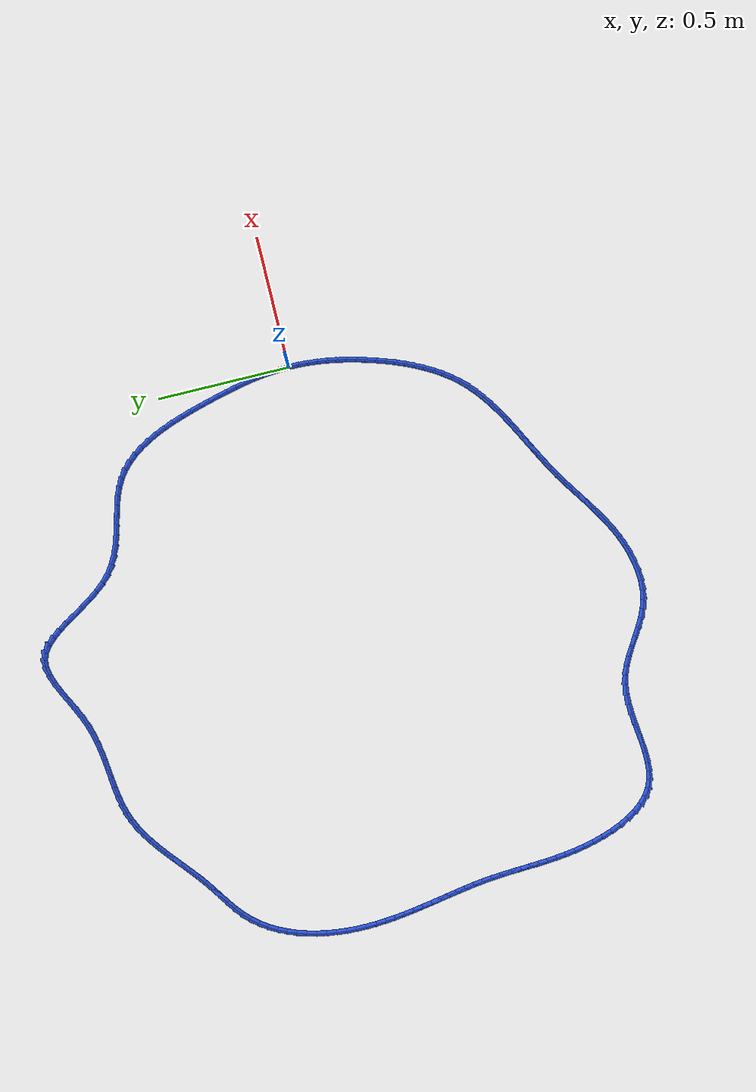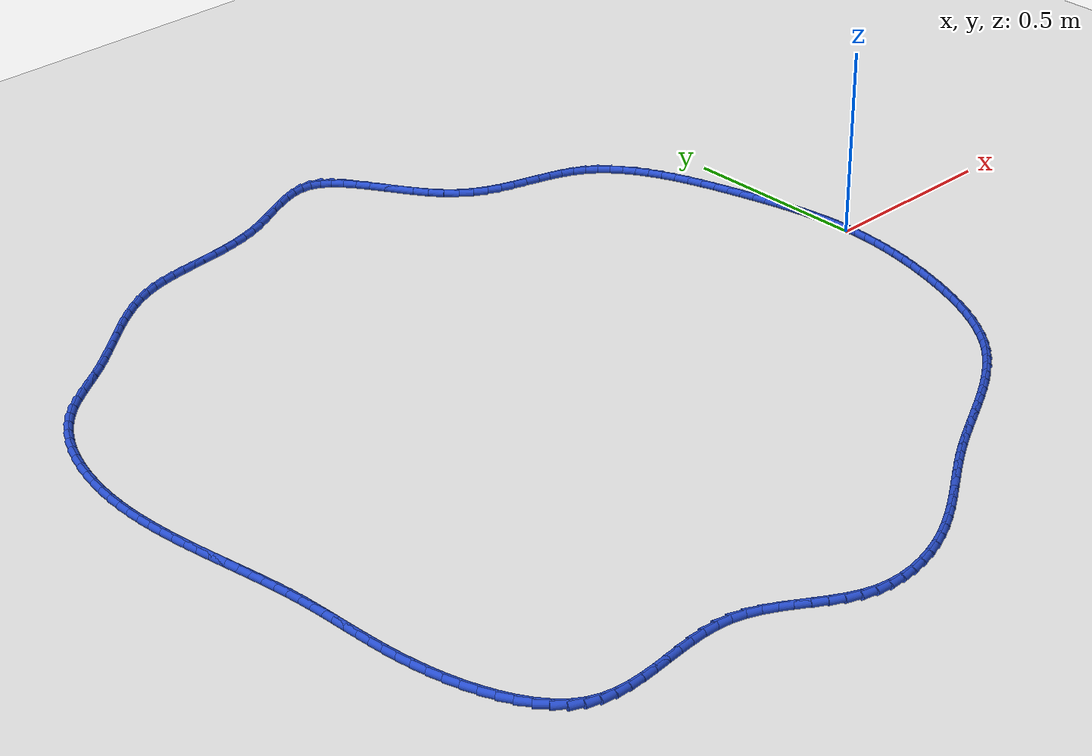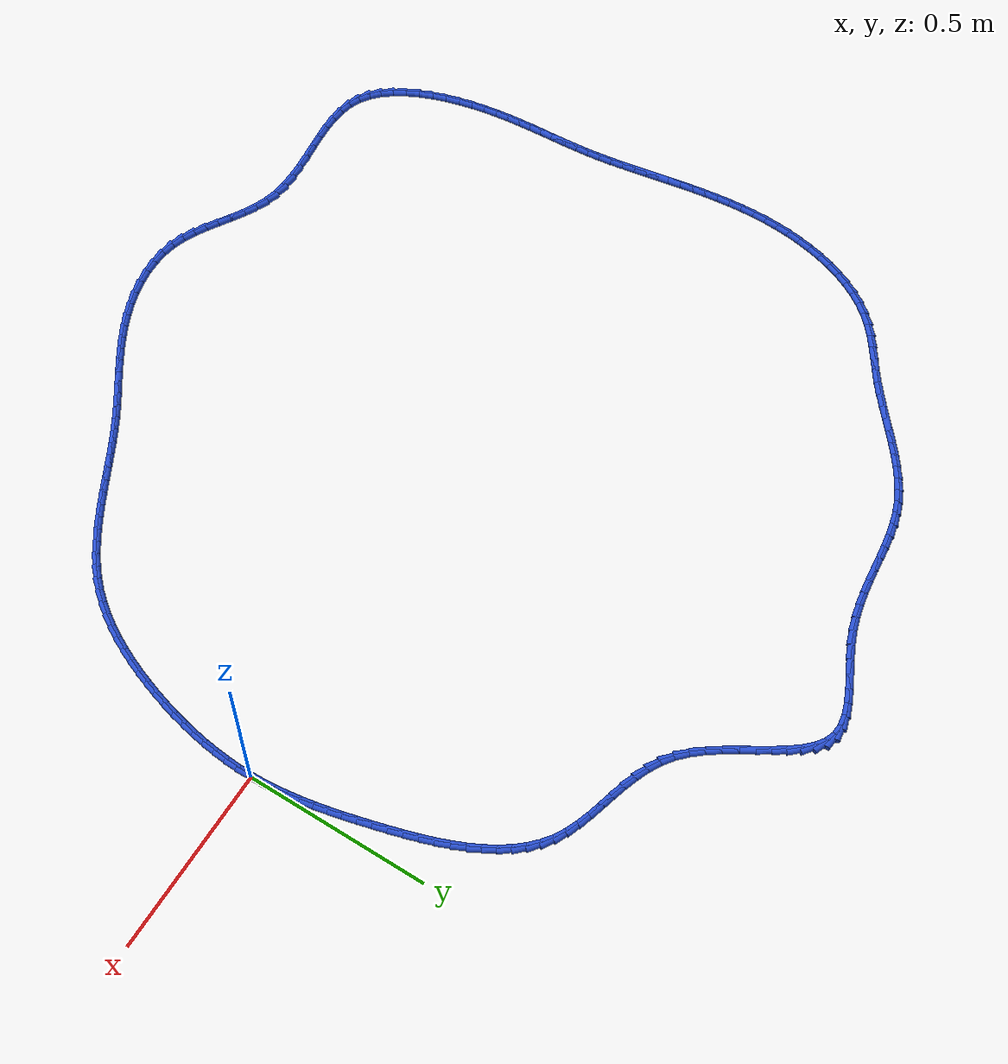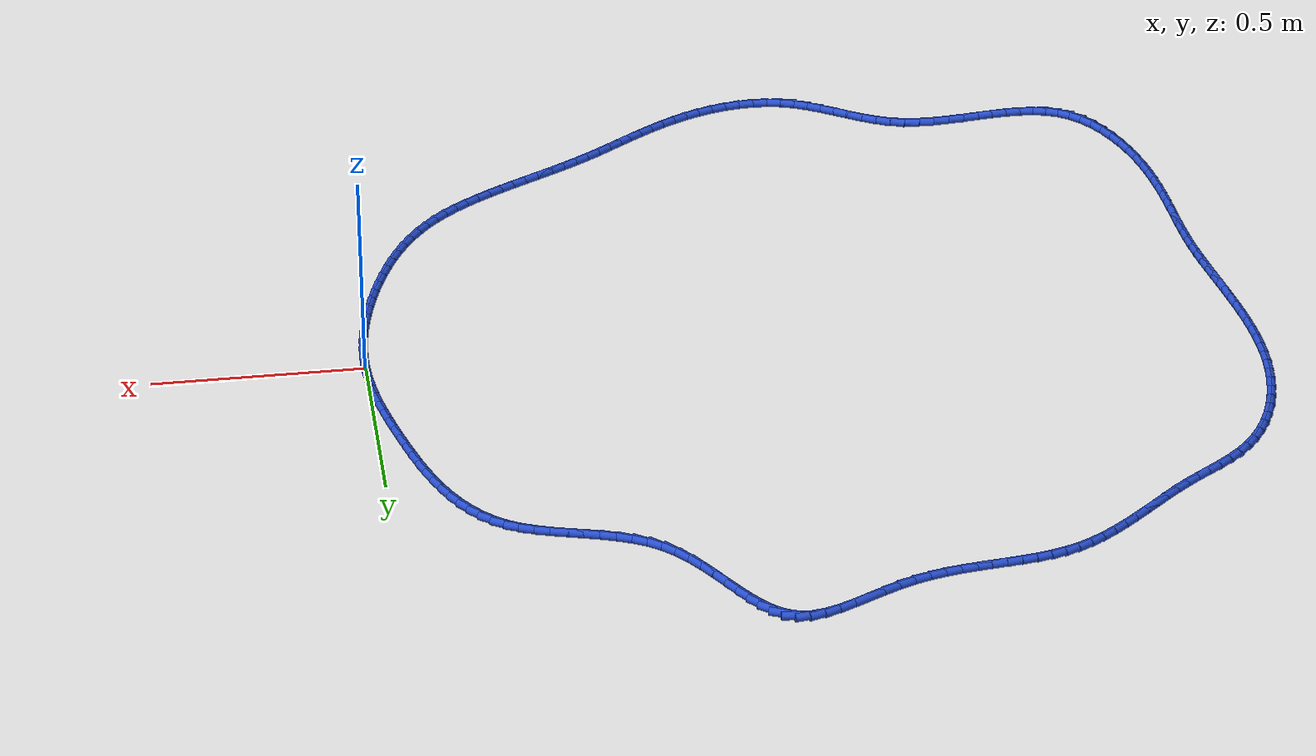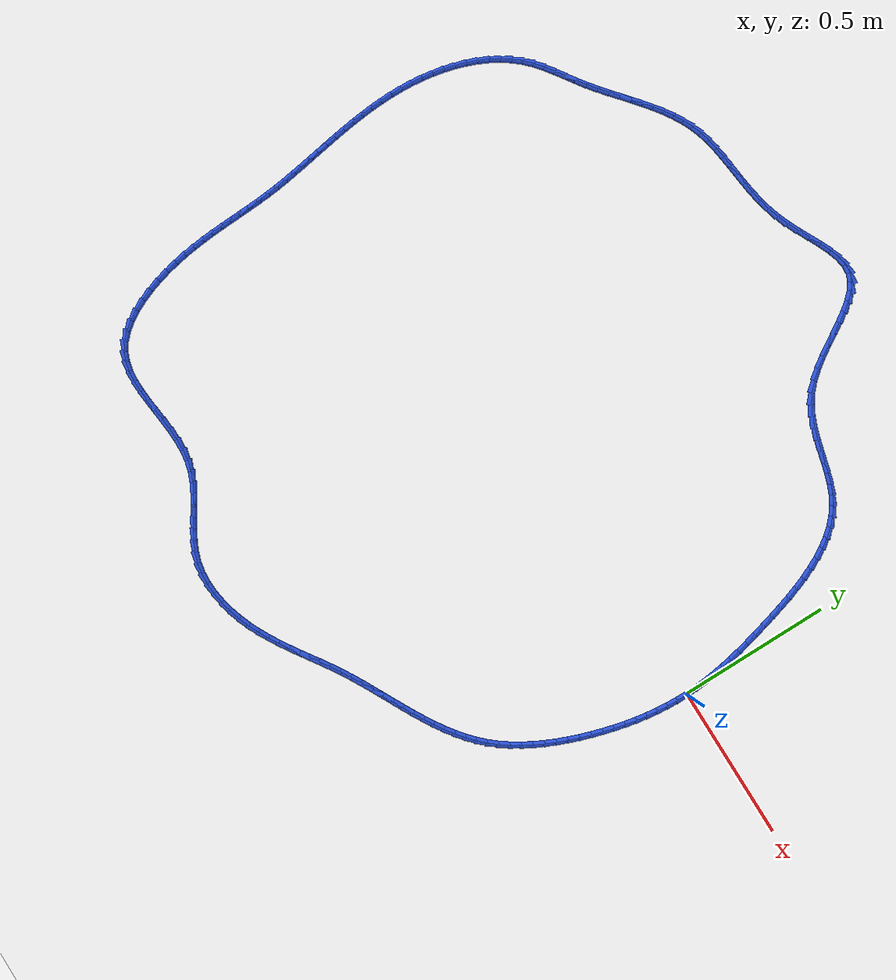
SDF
<sdf version="1.6">
 <world name="default">
  <light name="sun" type="directional">
   <pose>0 0 10 0 -0 0</pose>
   <diffuse>0.8 0.8 0.8 1</diffuse>
   <specular>0.2 0.2 0.2 1</specular>
   <attenuation>
    <range>1000</range>
    <constant>0.9</constant>
    <linear>0.01</linear>
    <quadratic>0.001</quadratic>
   </attenuation>
   <direction>-0.5 0.1 -0.9</direction>
  </light>
  <model name="ground_plane">
   <static>1</static>
   <link name="link">
    <collision name="collision">
     <geometry><plane><normal>0 0 1</normal><size>100 100</size></plane></geometry>
     <surface><friction><ode><mu>100</mu><mu2>50</mu2></ode></friction></surface>
    </collision>
    <visual name="visual">
     <cast_shadows>0</cast_shadows>
     <geometry><plane><normal>0 0 1</normal><size>100 100</size></plane></geometry>
     <material>
      <script><uri>file://media/materials/scripts/gazebo.material</uri><name>Gazebo/WhiteGlow</name></script>
     </material>
    </visual>
   </link>
  </model>
  <gravity>0 0 -9.8</gravity>
  <magnetic_field>6e-06 2.3e-05 -4.2e-05</magnetic_field>
  <atmosphere type="adiabatic"/>
  <physics name="default_physics" default="0" type="ode">
   <max_step_size>0.001</max_step_size>
   <real_time_factor>1</real_time_factor>
   <real_time_update_rate>1000</real_time_update_rate>
  </physics>
  <scene><ambient>0.4 0.4 0.4 1</ambient><background>0.7 0.7 0.7 1</background><shadows>1</shadows></scene>
  <spherical_coordinates>
   <surface_model>EARTH_WGS84</surface_model>
   <latitude_deg>0</latitude_deg>
   <longitude_deg>0</longitude_deg>
   <elevation>0</elevation>
   <heading_deg>0</heading_deg>
  </spherical_coordinates>
  <model name="line">
   <link name="link_0">
    <pose>-1.214306433183765e-17 9.020562075079397e-17 0.01 0 1.57 -1.5380622606158996</pose>
    <collision name="collision">
     <geometry><cylinder><radius>0.01</radius><length>0.08</length></cylinder></geometry>
    </collision>
    <visual name="visual">
     <material>
      <script><name>Gazebo/Blue</name><uri>file://media/materials/scripts/gazebo.material</uri></script>
     </material>
     <geometry><cylinder><radius>0.01</radius><length>0.08</length></cylinder></geometry>
    </visual>
   </link>
   <link name="link_1">
    <pose>-0.0011506230612284894 0.03513807463007038 0.01 0 1.57 -1.496610817460994</pose>
    <collision name="collision">
     <geometry><cylinder><radius>0.01</radius><length>0.08</length></cylinder></geometry>
    </collision>
    <visual name="visual">
     <material>
      <script><name>Gazebo/Blue</name><uri>file://media/materials/scripts/gazebo.material</uri></script>
     </material>
     <geometry><cylinder><radius>0.01</radius><length>0.08</length></cylinder></geometry>
    </visual>
   </link>
   <link name="link_2">
    <pose>-0.0037538692371258536 0.07016470988369111 0.01 0 1.57 -1.4587520466387607</pose>
    <collision name="collision">
     <geometry><cylinder><radius>0.01</radius><length>0.08</length></cylinder></geometry>
    </collision>
    <visual name="visual">
     <material>
      <script><name>Gazebo/Blue</name><uri>file://media/materials/scripts/gazebo.material</uri></script>
     </material>
     <geometry><cylinder><radius>0.01</radius><length>0.08</length></cylinder></geometry>
    </visual>
   </link>
   <link name="link_3">
    <pose>-0.007691794820837743 0.10516366715586643 0.01 0 1.57 -1.4247978003058401</pose>
    <collision name="collision">
     <geometry><cylinder><radius>0.01</radius><length>0.08</length></cylinder></geometry>
    </collision>
    <visual name="visual">
     <material>
      <script><name>Gazebo/Blue</name><uri>file://media/materials/scripts/gazebo.material</uri></script>
     </material>
     <geometry><cylinder><radius>0.01</radius><length>0.08</length></cylinder></geometry>
    </visual>
   </link>
   <link name="link_4">
    <pose>-0.012846456105509796 0.14021870784160032 0.01 0 1.57 -1.394950768331338</pose>
    <collision name="collision">
     <geometry><cylinder><radius>0.01</radius><length>0.08</length></cylinder></geometry>
    </collision>
    <visual name="visual">
     <material>
      <script><name>Gazebo/Blue</name><uri>file://media/materials/scripts/gazebo.material</uri></script>
     </material>
     <geometry><cylinder><radius>0.01</radius><length>0.08</length></cylinder></geometry>
    </visual>
   </link>
   <link name="link_5">
    <pose>-0.019099909384287645 0.1754135933358968 0.01 0 1.57 -1.3693155655176366</pose>
    <collision name="collision">
     <geometry><cylinder><radius>0.01</radius><length>0.08</length></cylinder></geometry>
    </collision>
    <visual name="visual">
     <material>
      <script><name>Gazebo/Blue</name><uri>file://media/materials/scripts/gazebo.material</uri></script>
     </material>
     <geometry><cylinder><radius>0.01</radius><length>0.08</length></cylinder></geometry>
    </visual>
   </link>
   <link name="link_6">
    <pose>-0.026334210950316926 0.21083208503375994 0.01 0 1.57 -1.3479135404917968</pose>
    <collision name="collision">
     <geometry><cylinder><radius>0.01</radius><length>0.08</length></cylinder></geometry>
    </collision>
    <visual name="visual">
     <material>
      <script><name>Gazebo/Blue</name><uri>file://media/materials/scripts/gazebo.material</uri></script>
     </material>
     <geometry><cylinder><radius>0.01</radius><length>0.08</length></cylinder></geometry>
    </visual>
   </link>
   <link name="link_7">
    <pose>-0.034431417096743265 0.24655794433019376 0.01 0 1.57 -1.3306987130496626</pose>
    <collision name="collision">
     <geometry><cylinder><radius>0.01</radius><length>0.08</length></cylinder></geometry>
    </collision>
    <visual name="visual">
     <material>
      <script><name>Gazebo/Blue</name><uri>file://media/materials/scripts/gazebo.material</uri></script>
     </material>
     <geometry><cylinder><radius>0.01</radius><length>0.08</length></cylinder></geometry>
    </visual>
   </link>
   <link name="link_8">
    <pose>-0.043273584116712324 0.2826749326202023 0.01 0 1.57 -1.317572950040889</pose>
    <collision name="collision">
     <geometry><cylinder><radius>0.01</radius><length>0.08</length></cylinder></geometry>
    </collision>
    <visual name="visual">
     <material>
      <script><name>Gazebo/Blue</name><uri>file://media/materials/scripts/gazebo.material</uri></script>
     </material>
     <geometry><cylinder><radius>0.01</radius><length>0.08</length></cylinder></geometry>
    </visual>
   </link>
   <link name="link_9">
    <pose>-0.052742768303369714 0.3192668112987897 0.01 0 1.57 -1.3073159627286455</pose>
    <collision name="collision">
     <geometry><cylinder><radius>0.01</radius><length>0.08</length></cylinder></geometry>
    </collision>
    <visual name="visual">
     <material>
      <script><name>Gazebo/Blue</name><uri>file://media/materials/scripts/gazebo.material</uri></script>
     </material>
     <geometry><cylinder><radius>0.01</radius><length>0.08</length></cylinder></geometry>
    </visual>
   </link>
   <link name="link_10">
    <pose>-0.06275183961175235 0.35637157240728556 0.01 0 1.57 -1.293049773808524</pose>
    <collision name="collision">
     <geometry><cylinder><radius>0.01</radius><length>0.08</length></cylinder></geometry>
    </collision>
    <visual name="visual">
     <material>
      <script><name>Gazebo/Blue</name><uri>file://media/materials/scripts/gazebo.material</uri></script>
     </material>
     <geometry><cylinder><radius>0.01</radius><length>0.08</length></cylinder></geometry>
    </visual>
   </link>
   <link name="link_11">
    <pose>-0.07340643263303766 0.39374088327694295 0.01 0 1.57 -1.2720303084117195</pose>
    <collision name="collision">
     <geometry><cylinder><radius>0.01</radius><length>0.08</length></cylinder></geometry>
    </collision>
    <visual name="visual">
     <material>
      <script><name>Gazebo/Blue</name><uri>file://media/materials/scripts/gazebo.material</uri></script>
     </material>
     <geometry><cylinder><radius>0.01</radius><length>0.08</length></cylinder></geometry>
    </visual>
   </link>
   <link name="link_12">
    <pose>-0.08488657225573862 0.431015914932516 0.01 0 1.57 -1.2438736644466282</pose>
    <collision name="collision">
     <geometry><cylinder><radius>0.01</radius><length>0.08</length></cylinder></geometry>
    </collision>
    <visual name="visual">
     <material>
      <script><name>Gazebo/Blue</name><uri>file://media/materials/scripts/gazebo.material</uri></script>
     </material>
     <geometry><cylinder><radius>0.01</radius><length>0.08</length></cylinder></geometry>
    </visual>
   </link>
   <link name="link_13">
    <pose>-0.0973724419508331 0.46783760284684867 0.01 0 1.57 -1.207934310243819</pose>
    <collision name="collision">
     <geometry><cylinder><radius>0.01</radius><length>0.08</length></cylinder></geometry>
    </collision>
    <visual name="visual">
     <material>
      <script><name>Gazebo/Blue</name><uri>file://media/materials/scripts/gazebo.material</uri></script>
     </material>
     <geometry><cylinder><radius>0.01</radius><length>0.08</length></cylinder></geometry>
    </visual>
   </link>
   <link name="link_14">
    <pose>-0.11104422518929906 0.5038468824927846 0.01 0 1.57 -1.1633031702608532</pose>
    <collision name="collision">
     <geometry><cylinder><radius>0.01</radius><length>0.08</length></cylinder></geometry>
    </collision>
    <visual name="visual">
     <material>
      <script><name>Gazebo/Blue</name><uri>file://media/materials/scripts/gazebo.material</uri></script>
     </material>
     <geometry><cylinder><radius>0.01</radius><length>0.08</length></cylinder></geometry>
    </visual>
   </link>
   <link name="link_15">
    <pose>-0.12608210544211448 0.5386846893431677 0.01 0 1.57 -1.1088187910350338</pose>
    <collision name="collision">
     <geometry><cylinder><radius>0.01</radius><length>0.08</length></cylinder></geometry>
    </collision>
    <visual name="visual">
     <material>
      <script><name>Gazebo/Blue</name><uri>file://media/materials/scripts/gazebo.material</uri></script>
     </material>
     <geometry><cylinder><radius>0.01</radius><length>0.08</length></cylinder></geometry>
    </visual>
   </link>
   <link name="link_16">
    <pose>-0.1426662661802572 0.5719919588708416 0.01 0 1.57 -1.0431102051470291</pose>
    <collision name="collision">
     <geometry><cylinder><radius>0.01</radius><length>0.08</length></cylinder></geometry>
    </collision>
    <visual name="visual">
     <material>
      <script><name>Gazebo/Blue</name><uri>file://media/materials/scripts/gazebo.material</uri></script>
     </material>
     <geometry><cylinder><radius>0.01</radius><length>0.08</length></cylinder></geometry>
    </visual>
   </link>
   <link name="link_17">
    <pose>-0.1609768908747053 0.6034096265486504 0.01 0 1.57 -0.9647107659040579</pose>
    <collision name="collision">
     <geometry><cylinder><radius>0.01</radius><length>0.08</length></cylinder></geometry>
    </collision>
    <visual name="visual">
     <material>
      <script><name>Gazebo/Blue</name><uri>file://media/materials/scripts/gazebo.material</uri></script>
     </material>
     <geometry><cylinder><radius>0.01</radius><length>0.08</length></cylinder></geometry>
    </visual>
   </link>
   <link name="link_18">
    <pose>-0.18119416299643654 0.6325786278494375 0.01 0 1.57 -0.8722990770588438</pose>
    <collision name="collision">
     <geometry><cylinder><radius>0.01</radius><length>0.08</length></cylinder></geometry>
    </collision>
    <visual name="visual">
     <material>
      <script><name>Gazebo/Blue</name><uri>file://media/materials/scripts/gazebo.material</uri></script>
     </material>
     <geometry><cylinder><radius>0.01</radius><length>0.08</length></cylinder></geometry>
    </visual>
   </link>
   <link name="link_19">
    <pose>-0.20349826601642895 0.6591398982460469 0.01 0 1.57 -0.7651241760697677</pose>
    <collision name="collision">
     <geometry><cylinder><radius>0.01</radius><length>0.08</length></cylinder></geometry>
    </collision>
    <visual name="visual">
     <material>
      <script><name>Gazebo/Blue</name><uri>file://media/materials/scripts/gazebo.material</uri></script>
     </material>
     <geometry><cylinder><radius>0.01</radius><length>0.08</length></cylinder></geometry>
    </visual>
   </link>
   <link name="link_20">
    <pose>-0.2280693834056605 0.6827343732113224 0.01 0 1.57 -0.6436166609132487</pose>
    <collision name="collision">
     <geometry><cylinder><radius>0.01</radius><length>0.08</length></cylinder></geometry>
    </collision>
    <visual name="visual">
     <material>
      <script><name>Gazebo/Blue</name><uri>file://media/materials/scripts/gazebo.material</uri></script>
     </material>
     <geometry><cylinder><radius>0.01</radius><length>0.08</length></cylinder></geometry>
    </visual>
   </link>
   <link name="link_21">
    <pose>-0.25508769863510905 0.7030029882181077 0.01 0 1.57 -0.5128015331279259</pose>
    <collision name="collision">
     <geometry><cylinder><radius>0.01</radius><length>0.08</length></cylinder></geometry>
    </collision>
    <visual name="visual">
     <material>
      <script><name>Gazebo/Blue</name><uri>file://media/materials/scripts/gazebo.material</uri></script>
     </material>
     <geometry><cylinder><radius>0.01</radius><length>0.08</length></cylinder></geometry>
    </visual>
   </link>
   <link name="link_22">
    <pose>-0.28468648842035343 0.7196683672140995 0.01 0 1.57 -0.4019532033720319</pose>
    <collision name="collision">
     <geometry><cylinder><radius>0.01</radius><length>0.08</length></cylinder></geometry>
    </collision>
    <visual name="visual">
     <material>
      <script><name>Gazebo/Blue</name><uri>file://media/materials/scripts/gazebo.material</uri></script>
     </material>
     <geometry><cylinder><radius>0.01</radius><length>0.08</length></cylinder></geometry>
    </visual>
   </link>
   <link name="link_23">
    <pose>-0.31655999583431965 0.7332177146082128 0.01 0 1.57 -0.3254217992859664</pose>
    <collision name="collision">
     <geometry><cylinder><radius>0.01</radius><length>0.08</length></cylinder></geometry>
    </collision>
    <visual name="visual">
     <material>
      <script><name>Gazebo/Blue</name><uri>file://media/materials/scripts/gazebo.material</uri></script>
     </material>
     <geometry><cylinder><radius>0.01</radius><length>0.08</length></cylinder></geometry>
    </visual>
   </link>
   <link name="link_24">
    <pose>-0.3501626664106306 0.744555844066119 0.01 0 1.57 -0.2808949452889704</pose>
    <collision name="collision">
     <geometry><cylinder><radius>0.01</radius><length>0.08</length></cylinder></geometry>
    </collision>
    <visual name="visual">
     <material>
      <script><name>Gazebo/Blue</name><uri>file://media/materials/scripts/gazebo.material</uri></script>
     </material>
     <geometry><cylinder><radius>0.01</radius><length>0.08</length></cylinder></geometry>
    </visual>
   </link>
   <link name="link_25">
    <pose>-0.3849465148790331 0.754591802517114 0.01 0 1.57 -0.2658220890735063</pose>
    <collision name="collision">
     <geometry><cylinder><radius>0.01</radius><length>0.08</length></cylinder></geometry>
    </collision>
    <visual name="visual">
     <material>
      <script><name>Gazebo/Blue</name><uri>file://media/materials/scripts/gazebo.material</uri></script>
     </material>
     <geometry><cylinder><radius>0.01</radius><length>0.08</length></cylinder></geometry>
    </visual>
   </link>
   <link name="link_26">
    <pose>-0.4203635559692735 0.7642346368904932 0.01 0 1.57 -0.2786969449983281</pose>
    <collision name="collision">
     <geometry><cylinder><radius>0.01</radius><length>0.08</length></cylinder></geometry>
    </collision>
    <visual name="visual">
     <material>
      <script><name>Gazebo/Blue</name><uri>file://media/materials/scripts/gazebo.material</uri></script>
     </material>
     <geometry><cylinder><radius>0.01</radius><length>0.08</length></cylinder></geometry>
    </visual>
   </link>
   <link name="link_27">
    <pose>-0.45586580441109825 0.7743933941155521 0.01 0 1.57 -0.31928025760383244</pose>
    <collision name="collision">
     <geometry><cylinder><radius>0.01</radius><length>0.08</length></cylinder></geometry>
    </collision>
    <visual name="visual">
     <material>
      <script><name>Gazebo/Blue</name><uri>file://media/materials/scripts/gazebo.material</uri></script>
     </material>
     <geometry><cylinder><radius>0.01</radius><length>0.08</length></cylinder></geometry>
    </visual>
   </link>
   <link name="link_28">
    <pose>-0.4909052749342538 0.7859771211215861 0.01 0 1.57 -0.3882409004246865</pose>
    <collision name="collision">
     <geometry><cylinder><radius>0.01</radius><length>0.08</length></cylinder></geometry>
    </collision>
    <visual name="visual">
     <material>
      <script><name>Gazebo/Blue</name><uri>file://media/materials/scripts/gazebo.material</uri></script>
     </material>
     <geometry><cylinder><radius>0.01</radius><length>0.08</length></cylinder></geometry>
    </visual>
   </link>
   <link name="link_29">
    <pose>-0.524933982268487 0.7998948648378911 0.01 0 1.57 -0.4861972512409532</pose>
    <collision name="collision">
     <geometry><cylinder><radius>0.01</radius><length>0.08</length></cylinder></geometry>
    </collision>
    <visual name="visual">
     <material>
      <script><name>Gazebo/Blue</name><uri>file://media/materials/scripts/gazebo.material</uri></script>
     </material>
     <geometry><cylinder><radius>0.01</radius><length>0.08</length></cylinder></geometry>
    </visual>
   </link>
   <link name="link_30">
    <pose>-0.5574039411435436 0.8170556721937619 0.01 0 1.57 -0.6120214006155447</pose>
    <collision name="collision">
     <geometry><cylinder><radius>0.01</radius><length>0.08</length></cylinder></geometry>
    </collision>
    <visual name="visual">
     <material>
      <script><name>Gazebo/Blue</name><uri>file://media/materials/scripts/gazebo.material</uri></script>
     </material>
     <geometry><cylinder><radius>0.01</radius><length>0.08</length></cylinder></geometry>
    </visual>
   </link>
   <link name="link_31">
    <pose>-0.5877671662891709 0.8383685901184947 0.01 0 1.57 -0.753441485325637</pose>
    <collision name="collision">
     <geometry><cylinder><radius>0.01</radius><length>0.08</length></cylinder></geometry>
    </collision>
    <visual name="visual">
     <material>
      <script><name>Gazebo/Blue</name><uri>file://media/materials/scripts/gazebo.material</uri></script>
     </material>
     <geometry><cylinder><radius>0.01</radius><length>0.08</length></cylinder></geometry>
    </visual>
   </link>
   <link name="link_32">
    <pose>-0.6156007514404964 0.8644777570581857 0.01 0 1.57 -0.8675343127788963</pose>
    <collision name="collision">
     <geometry><cylinder><radius>0.01</radius><length>0.08</length></cylinder></geometry>
    </collision>
    <visual name="visual">
     <material>
      <script><name>Gazebo/Blue</name><uri>file://media/materials/scripts/gazebo.material</uri></script>
     </material>
     <geometry><cylinder><radius>0.01</radius><length>0.08</length></cylinder></geometry>
    </visual>
   </link>
   <link name="link_33">
    <pose>-0.6411503757834095 0.8946112947812314 0.01 0 1.57 -0.9460708070805375</pose>
    <collision name="collision">
     <geometry><cylinder><radius>0.01</radius><length>0.08</length></cylinder></geometry>
    </collision>
    <visual name="visual">
     <material>
      <script><name>Gazebo/Blue</name><uri>file://media/materials/scripts/gazebo.material</uri></script>
     </material>
     <geometry><cylinder><radius>0.01</radius><length>0.08</length></cylinder></geometry>
    </visual>
   </link>
   <link name="link_34">
    <pose>-0.6648841917305175 0.9275261425033503 0.01 0 1.57 -0.994584265589209</pose>
    <collision name="collision">
     <geometry><cylinder><radius>0.01</radius><length>0.08</length></cylinder></geometry>
    </collision>
    <visual name="visual">
     <material>
      <script><name>Gazebo/Blue</name><uri>file://media/materials/scripts/gazebo.material</uri></script>
     </material>
     <geometry><cylinder><radius>0.01</radius><length>0.08</length></cylinder></geometry>
    </visual>
   </link>
   <link name="link_35">
    <pose>-0.6872705021589269 0.9619789207670965 0.01 0 1.57 -1.016554241169779</pose>
    <collision name="collision">
     <geometry><cylinder><radius>0.01</radius><length>0.08</length></cylinder></geometry>
    </collision>
    <visual name="visual">
     <material>
      <script><name>Gazebo/Blue</name><uri>file://media/materials/scripts/gazebo.material</uri></script>
     </material>
     <geometry><cylinder><radius>0.01</radius><length>0.08</length></cylinder></geometry>
    </visual>
   </link>
   <link name="link_36">
    <pose>-0.7087776099457439 0.9967262501150247 0.01 0 1.57 -1.0127898792860328</pose>
    <collision name="collision">
     <geometry><cylinder><radius>0.01</radius><length>0.08</length></cylinder></geometry>
    </collision>
    <visual name="visual">
     <material>
      <script><name>Gazebo/Blue</name><uri>file://media/materials/scripts/gazebo.material</uri></script>
     </material>
     <geometry><cylinder><radius>0.01</radius><length>0.08</length></cylinder></geometry>
    </visual>
   </link>
   <link name="link_37">
    <pose>-0.729873817968075 1.030524751089689 0.01 0 1.57 -0.980983368816893</pose>
    <collision name="collision">
     <geometry><cylinder><radius>0.01</radius><length>0.08</length></cylinder></geometry>
    </collision>
    <visual name="visual">
     <material>
      <script><name>Gazebo/Blue</name><uri>file://media/materials/scripts/gazebo.material</uri></script>
     </material>
     <geometry><cylinder><radius>0.01</radius><length>0.08</length></cylinder></geometry>
    </visual>
   </link>
   <link name="link_38">
    <pose>-0.7510274291030271 1.062131044233645 0.01 0 1.57 -0.9148879022112547</pose>
    <collision name="collision">
     <geometry><cylinder><radius>0.01</radius><length>0.08</length></cylinder></geometry>
    </collision>
    <visual name="visual">
     <material>
      <script><name>Gazebo/Blue</name><uri>file://media/materials/scripts/gazebo.material</uri></script>
     </material>
     <geometry><cylinder><radius>0.01</radius><length>0.08</length></cylinder></geometry>
    </visual>
   </link>
   <link name="link_39">
    <pose>-0.7727067462277065 1.090301750089446 0.01 0 1.57 -0.8031242815300945</pose>
    <collision name="collision">
     <geometry><cylinder><radius>0.01</radius><length>0.08</length></cylinder></geometry>
    </collision>
    <visual name="visual">
     <material>
      <script><name>Gazebo/Blue</name><uri>file://media/materials/scripts/gazebo.material</uri></script>
     </material>
     <geometry><cylinder><radius>0.01</radius><length>0.08</length></cylinder></geometry>
    </visual>
   </link>
   <link name="link_40">
    <pose>-0.7953800722192195 1.113793489199647 0.01 0 1.57 -0.6292352011571766</pose>
    <collision name="collision">
     <geometry><cylinder><radius>0.01</radius><length>0.08</length></cylinder></geometry>
    </collision>
    <visual name="visual">
     <material>
      <script><name>Gazebo/Blue</name><uri>file://media/materials/scripts/gazebo.material</uri></script>
     </material>
     <geometry><cylinder><radius>0.01</radius><length>0.08</length></cylinder></geometry>
    </visual>
   </link>
   <link name="link_41">
    <pose>-0.8195157099546727 1.1313628821068027 0.01 0 1.57 -0.37975098794788187</pose>
    <collision name="collision">
     <geometry><cylinder><radius>0.01</radius><length>0.08</length></cylinder></geometry>
    </collision>
    <visual name="visual">
     <material>
      <script><name>Gazebo/Blue</name><uri>file://media/materials/scripts/gazebo.material</uri></script>
     </material>
     <geometry><cylinder><radius>0.01</radius><length>0.08</length></cylinder></geometry>
    </visual>
   </link>
   <link name="link_42">
    <pose>-0.8455819623111727 1.1417665493534672 0.01 0 1.57 -0.08009483085022656</pose>
    <collision name="collision">
     <geometry><cylinder><radius>0.01</radius><length>0.08</length></cylinder></geometry>
    </collision>
    <visual name="visual">
     <material>
      <script><name>Gazebo/Blue</name><uri>file://media/materials/scripts/gazebo.material</uri></script>
     </material>
     <geometry><cylinder><radius>0.01</radius><length>0.08</length></cylinder></geometry>
    </visual>
   </link>
   <link name="link_43">
    <pose>-0.873968294174791 1.1440450221601086 0.01 0 1.57 0.1611885504679022</pose>
    <collision name="collision">
     <geometry><cylinder><radius>0.01</radius><length>0.08</length></cylinder></geometry>
    </collision>
    <visual name="visual">
     <material>
      <script><name>Gazebo/Blue</name><uri>file://media/materials/scripts/gazebo.material</uri></script>
     </material>
     <geometry><cylinder><radius>0.01</radius><length>0.08</length></cylinder></geometry>
    </visual>
   </link>
   <link name="link_44">
    <pose>-0.9045552336822972 1.139071610279652 0.01 0 1.57 0.31625287087366766</pose>
    <collision name="collision">
     <geometry><cylinder><radius>0.01</radius><length>0.08</length></cylinder></geometry>
    </collision>
    <visual name="visual">
     <material>
      <script><name>Gazebo/Blue</name><uri>file://media/materials/scripts/gazebo.material</uri></script>
     </material>
     <geometry><cylinder><radius>0.01</radius><length>0.08</length></cylinder></geometry>
    </visual>
   </link>
   <link name="link_45">
    <pose>-0.9370211621901585 1.1284475926671778 0.01 0 1.57 0.40713198622387126</pose>
    <collision name="collision">
     <geometry><cylinder><radius>0.01</radius><length>0.08</length></cylinder></geometry>
    </collision>
    <visual name="visual">
     <material>
      <script><name>Gazebo/Blue</name><uri>file://media/materials/scripts/gazebo.material</uri></script>
     </material>
     <geometry><cylinder><radius>0.01</radius><length>0.08</length></cylinder></geometry>
    </visual>
   </link>
   <link name="link_46">
    <pose>-0.971043948323818 1.1137760947202167 0.01 0 1.57 0.4519421486328973</pose>
    <collision name="collision">
     <geometry><cylinder><radius>0.01</radius><length>0.08</length></cylinder></geometry>
    </collision>
    <visual name="visual">
     <material>
      <script><name>Gazebo/Blue</name><uri>file://media/materials/scripts/gazebo.material</uri></script>
     </material>
     <geometry><cylinder><radius>0.01</radius><length>0.08</length></cylinder></geometry>
    </visual>
   </link>
   <link name="link_47">
    <pose>-1.0063014607087177 1.0966602418362992 0.01 0 1.57 0.46081317499080354</pose>
    <collision name="collision">
     <geometry><cylinder><radius>0.01</radius><length>0.08</length></cylinder></geometry>
    </collision>
    <visual name="visual">
     <material>
      <script><name>Gazebo/Blue</name><uri>file://media/materials/scripts/gazebo.material</uri></script>
     </material>
     <geometry><cylinder><radius>0.01</radius><length>0.08</length></cylinder></geometry>
    </visual>
   </link>
   <link name="link_48">
    <pose>-1.0424715679702994 1.0787031594129544 0.01 0 1.57 0.43752597725870535</pose>
    <collision name="collision">
     <geometry><cylinder><radius>0.01</radius><length>0.08</length></cylinder></geometry>
    </collision>
    <visual name="visual">
     <material>
      <script><name>Gazebo/Blue</name><uri>file://media/materials/scripts/gazebo.material</uri></script>
     </material>
     <geometry><cylinder><radius>0.01</radius><length>0.08</length></cylinder></geometry>
    </visual>
   </link>
   <link name="link_49">
    <pose>-1.0792321387340058 1.0615079728477146 0.01 0 1.57 0.3810806210362158</pose>
    <collision name="collision">
     <geometry><cylinder><radius>0.01</radius><length>0.08</length></cylinder></geometry>
    </collision>
    <visual name="visual">
     <material>
      <script><name>Gazebo/Blue</name><uri>file://media/materials/scripts/gazebo.material</uri></script>
     </material>
     <geometry><cylinder><radius>0.01</radius><length>0.08</length></cylinder></geometry>
    </visual>
   </link>
   <link name="link_50">
    <pose>-1.1162616862994799 1.046671481920214 0.01 0 1.57 0.303224469950522</pose>
    <collision name="collision">
     <geometry><cylinder><radius>0.01</radius><length>0.08</length></cylinder></geometry>
    </collision>
    <visual name="visual">
     <material>
      <script><name>Gazebo/Blue</name><uri>file://media/materials/scripts/gazebo.material</uri></script>
     </material>
     <geometry><cylinder><radius>0.01</radius><length>0.08</length></cylinder></geometry>
    </visual>
   </link>
   <link name="link_51">
    <pose>-1.1533111627913597 1.035079708272695 0.01 0 1.57 0.23408802881667748</pose>
    <collision name="collision">
     <geometry><cylinder><radius>0.01</radius><length>0.08</length></cylinder></geometry>
    </collision>
    <visual name="visual">
     <material>
      <script><name>Gazebo/Blue</name><uri>file://media/materials/scripts/gazebo.material</uri></script>
     </material>
     <geometry><cylinder><radius>0.01</radius><length>0.08</length></cylinder></geometry>
    </visual>
   </link>
   <link name="link_52">
    <pose>-1.1902693083842475 1.0262666812488401 0.01 0 1.57 0.1789597366316025</pose>
    <collision name="collision">
     <geometry><cylinder><radius>0.01</radius><length>0.08</length></cylinder></geometry>
    </collision>
    <visual name="visual">
     <material>
      <script><name>Gazebo/Blue</name><uri>file://media/materials/scripts/gazebo.material</uri></script>
     </material>
     <geometry><cylinder><radius>0.01</radius><length>0.08</length></cylinder></geometry>
    </visual>
   </link>
   <link name="link_53">
    <pose>-1.2270402970044634 1.019614992433661 0.01 0 1.57 0.13908084169282445</pose>
    <collision name="collision">
     <geometry><cylinder><radius>0.01</radius><length>0.08</length></cylinder></geometry>
    </collision>
    <visual name="visual">
     <material>
      <script><name>Gazebo/Blue</name><uri>file://media/materials/scripts/gazebo.material</uri></script>
     </material>
     <geometry><cylinder><radius>0.01</radius><length>0.08</length></cylinder></geometry>
    </visual>
   </link>
   <link name="link_54">
    <pose>-1.2635283025783266 1.0145072334121663 0.01 0 1.57 0.11528084787527913</pose>
    <collision name="collision">
     <geometry><cylinder><radius>0.01</radius><length>0.08</length></cylinder></geometry>
    </collision>
    <visual name="visual">
     <material>
      <script><name>Gazebo/Blue</name><uri>file://media/materials/scripts/gazebo.material</uri></script>
     </material>
     <geometry><cylinder><radius>0.01</radius><length>0.08</length></cylinder></geometry>
    </visual>
   </link>
   <link name="link_55">
    <pose>-1.2996374990321566 1.0103259957693682 0.01 0 1.57 0.10823738652672818</pose>
    <collision name="collision">
     <geometry><cylinder><radius>0.01</radius><length>0.08</length></cylinder></geometry>
    </collision>
    <visual name="visual">
     <material>
      <script><name>Gazebo/Blue</name><uri>file://media/materials/scripts/gazebo.material</uri></script>
     </material>
     <geometry><cylinder><radius>0.01</radius><length>0.08</length></cylinder></geometry>
    </visual>
   </link>
   <link name="link_56">
    <pose>-1.3352720602922732 1.0064538710902768 0.01 0 1.57 0.1186621247251264</pose>
    <collision name="collision">
     <geometry><cylinder><radius>0.01</radius><length>0.08</length></cylinder></geometry>
    </collision>
    <visual name="visual">
     <material>
      <script><name>Gazebo/Blue</name><uri>file://media/materials/scripts/gazebo.material</uri></script>
     </material>
     <geometry><cylinder><radius>0.01</radius><length>0.08</length></cylinder></geometry>
    </visual>
   </link>
   <link name="link_57">
    <pose>-1.3703361602849955 1.0022734509599025 0.01 0 1.57 0.14736713254396594</pose>
    <collision name="collision">
     <geometry><cylinder><radius>0.01</radius><length>0.08</length></cylinder></geometry>
    </collision>
    <visual name="visual">
     <material>
      <script><name>Gazebo/Blue</name><uri>file://media/materials/scripts/gazebo.material</uri></script>
     </material>
     <geometry><cylinder><radius>0.01</radius><length>0.08</length></cylinder></geometry>
    </visual>
   </link>
   <link name="link_58">
    <pose>-1.404733972936643 0.9971673269632568 0.01 0 1.57 0.1951675540446862</pose>
    <collision name="collision">
     <geometry><cylinder><radius>0.01</radius><length>0.08</length></cylinder></geometry>
    </collision>
    <visual name="visual">
     <material>
      <script><name>Gazebo/Blue</name><uri>file://media/materials/scripts/gazebo.material</uri></script>
     </material>
     <geometry><cylinder><radius>0.01</radius><length>0.08</length></cylinder></geometry>
    </visual>
   </link>
   <link name="link_59">
    <pose>-1.438369672173536 0.99051809068535 0.01 0 1.57 0.2625672876067255</pose>
    <collision name="collision">
     <geometry><cylinder><radius>0.01</radius><length>0.08</length></cylinder></geometry>
    </collision>
    <visual name="visual">
     <material>
      <script><name>Gazebo/Blue</name><uri>file://media/materials/scripts/gazebo.material</uri></script>
     </material>
     <geometry><cylinder><radius>0.01</radius><length>0.08</length></cylinder></geometry>
    </visual>
   </link>
   <link name="link_60">
    <pose>-1.4711474319219933 0.9817083337111924 0.01 0 1.57 0.34900589650083336</pose>
    <collision name="collision">
     <geometry><cylinder><radius>0.01</radius><length>0.08</length></cylinder></geometry>
    </collision>
    <visual name="visual">
     <material>
      <script><name>Gazebo/Blue</name><uri>file://media/materials/scripts/gazebo.material</uri></script>
     </material>
     <geometry><cylinder><radius>0.01</radius><length>0.08</length></cylinder></geometry>
    </visual>
   </link>
   <link name="link_61">
    <pose>-1.5029729566468835 0.9701269508080823 0.01 0 1.57 0.44118302864099646</pose>
    <collision name="collision">
     <geometry><cylinder><radius>0.01</radius><length>0.08</length></cylinder></geometry>
    </collision>
    <visual name="visual">
     <material>
      <script><name>Gazebo/Blue</name><uri>file://media/materials/scripts/gazebo.material</uri></script>
     </material>
     <geometry><cylinder><radius>0.01</radius><length>0.08</length></cylinder></geometry>
    </visual>
   </link>
   <link name="link_62">
    <pose>-1.5338455038266354 0.9555481140028372 0.01 0 1.57 0.5196706058859099</pose>
    <collision name="collision">
     <geometry><cylinder><radius>0.01</radius><length>0.08</length></cylinder></geometry>
    </collision>
    <visual name="visual">
     <material>
      <script><name>Gazebo/Blue</name><uri>file://media/materials/scripts/gazebo.material</uri></script>
     </material>
     <geometry><cylinder><radius>0.01</radius><length>0.08</length></cylinder></geometry>
    </visual>
   </link>
   <link name="link_63">
    <pose>-1.5639103362638402 0.9383472857460565 0.01 0 1.57 0.5829279601623156</pose>
    <collision name="collision">
     <geometry><cylinder><radius>0.01</radius><length>0.08</length></cylinder></geometry>
    </collision>
    <visual name="visual">
     <material>
      <script><name>Gazebo/Blue</name><uri>file://media/materials/scripts/gazebo.material</uri></script>
     </material>
     <geometry><cylinder><radius>0.01</radius><length>0.08</length></cylinder></geometry>
    </visual>
   </link>
   <link name="link_64">
    <pose>-1.5933253937488618 0.9189521358403244 0.01 0 1.57 0.6316561434028991</pose>
    <collision name="collision">
     <geometry><cylinder><radius>0.01</radius><length>0.08</length></cylinder></geometry>
    </collision>
    <visual name="visual">
     <material>
      <script><name>Gazebo/Blue</name><uri>file://media/materials/scripts/gazebo.material</uri></script>
     </material>
     <geometry><cylinder><radius>0.01</radius><length>0.08</length></cylinder></geometry>
    </visual>
   </link>
   <link name="link_65">
    <pose>-1.6222486160720644 0.8977903340882265 0.01 0 1.57 0.6667849364176438</pose>
    <collision name="collision">
     <geometry><cylinder><radius>0.01</radius><length>0.08</length></cylinder></geometry>
    </collision>
    <visual name="visual">
     <material>
      <script><name>Gazebo/Blue</name><uri>file://media/materials/scripts/gazebo.material</uri></script>
     </material>
     <geometry><cylinder><radius>0.01</radius><length>0.08</length></cylinder></geometry>
    </visual>
   </link>
   <link name="link_66">
    <pose>-1.6508379430238116 0.8752895502923481 0.01 0 1.57 0.6891937941548922</pose>
    <collision name="collision">
     <geometry><cylinder><radius>0.01</radius><length>0.08</length></cylinder></geometry>
    </collision>
    <visual name="visual">
     <material>
      <script><name>Gazebo/Blue</name><uri>file://media/materials/scripts/gazebo.material</uri></script>
     </material>
     <geometry><cylinder><radius>0.01</radius><length>0.08</length></cylinder></geometry>
    </visual>
   </link>
   <link name="link_67">
    <pose>-1.6792513143944692 0.8518774542552737 0.01 0 1.57 0.6995602121632418</pose>
    <collision name="collision">
     <geometry><cylinder><radius>0.01</radius><length>0.08</length></cylinder></geometry>
    </collision>
    <visual name="visual">
     <material>
      <script><name>Gazebo/Blue</name><uri>file://media/materials/scripts/gazebo.material</uri></script>
     </material>
     <geometry><cylinder><radius>0.01</radius><length>0.08</length></cylinder></geometry>
    </visual>
   </link>
   <link name="link_68">
    <pose>-1.7076466699744 0.8279817157795881 0.01 0 1.57 0.6982914383562189</pose>
    <collision name="collision">
     <geometry><cylinder><radius>0.01</radius><length>0.08</length></cylinder></geometry>
    </collision>
    <visual name="visual">
     <material>
      <script><name>Gazebo/Blue</name><uri>file://media/materials/scripts/gazebo.material</uri></script>
     </material>
     <geometry><cylinder><radius>0.01</radius><length>0.08</length></cylinder></geometry>
    </visual>
   </link>
   <link name="link_69">
    <pose>-1.736181949553969 0.8040300046678767 0.01 0 1.57 0.6855063519692556</pose>
    <collision name="collision">
     <geometry><cylinder><radius>0.01</radius><length>0.08</length></cylinder></geometry>
    </collision>
    <visual name="visual">
     <material>
      <script><name>Gazebo/Blue</name><uri>file://media/materials/scripts/gazebo.material</uri></script>
     </material>
     <geometry><cylinder><radius>0.01</radius><length>0.08</length></cylinder></geometry>
    </visual>
   </link>
   <link name="link_70">
    <pose>-1.76501509292354 0.7804499907227247 0.01 0 1.57 0.6610507188350221</pose>
    <collision name="collision">
     <geometry><cylinder><radius>0.01</radius><length>0.08</length></cylinder></geometry>
    </collision>
    <visual name="visual">
     <material>
      <script><name>Gazebo/Blue</name><uri>file://media/materials/scripts/gazebo.material</uri></script>
     </material>
     <geometry><cylinder><radius>0.01</radius><length>0.08</length></cylinder></geometry>
    </visual>
   </link>
   <link name="link_71">
    <pose>-1.7943040398734773 0.7576693437467167 0.01 0 1.57 0.626384147757348</pose>
    <collision name="collision">
     <geometry><cylinder><radius>0.01</radius><length>0.08</length></cylinder></geometry>
    </collision>
    <visual name="visual">
     <material>
      <script><name>Gazebo/Blue</name><uri>file://media/materials/scripts/gazebo.material</uri></script>
     </material>
     <geometry><cylinder><radius>0.01</radius><length>0.08</length></cylinder></geometry>
    </visual>
   </link>
   <link name="link_72">
    <pose>-1.8241697608329401 0.736058770939046 0.01 0 1.57 0.6030055812669212</pose>
    <collision name="collision">
     <geometry><cylinder><radius>0.01</radius><length>0.08</length></cylinder></geometry>
    </collision>
    <visual name="visual">
     <material>
      <script><name>Gazebo/Blue</name><uri>file://media/materials/scripts/gazebo.material</uri></script>
     </material>
     <geometry><cylinder><radius>0.01</radius><length>0.08</length></cylinder></geometry>
    </visual>
   </link>
   <link name="link_73">
    <pose>-1.8542959111928043 0.7153151619843369 0.01 0 1.57 0.60554564625939</pose>
    <collision name="collision">
     <geometry><cylinder><radius>0.01</radius><length>0.08</length></cylinder></geometry>
    </collision>
    <visual name="visual">
     <material>
      <script><name>Gazebo/Blue</name><uri>file://media/materials/scripts/gazebo.material</uri></script>
     </material>
     <geometry><cylinder><radius>0.01</radius><length>0.08</length></cylinder></geometry>
    </visual>
   </link>
   <link name="link_74">
    <pose>-1.8840803825407086 0.6946951000632103 0.01 0 1.57 0.6350295746790727</pose>
    <collision name="collision">
     <geometry><cylinder><radius>0.01</radius><length>0.08</length></cylinder></geometry>
    </collision>
    <visual name="visual">
     <material>
      <script><name>Gazebo/Blue</name><uri>file://media/materials/scripts/gazebo.material</uri></script>
     </material>
     <geometry><cylinder><radius>0.01</radius><length>0.08</length></cylinder></geometry>
    </visual>
   </link>
   <link name="link_75">
    <pose>-1.9129161381880415 0.6734475748400317 0.01 0 1.57 0.6924116914227368</pose>
    <collision name="collision">
     <geometry><cylinder><radius>0.01</radius><length>0.08</length></cylinder></geometry>
    </collision>
    <visual name="visual">
     <material>
      <script><name>Gazebo/Blue</name><uri>file://media/materials/scripts/gazebo.material</uri></script>
     </material>
     <geometry><cylinder><radius>0.01</radius><length>0.08</length></cylinder></geometry>
    </visual>
   </link>
   <link name="link_76">
    <pose>-1.9401961414461906 0.6508215759791649 0.01 0 1.57 0.7777512405550179</pose>
    <collision name="collision">
     <geometry><cylinder><radius>0.01</radius><length>0.08</length></cylinder></geometry>
    </collision>
    <visual name="visual">
     <material>
      <script><name>Gazebo/Blue</name><uri>file://media/materials/scripts/gazebo.material</uri></script>
     </material>
     <geometry><cylinder><radius>0.01</radius><length>0.08</length></cylinder></geometry>
    </visual>
   </link>
   <link name="link_77">
    <pose>-1.9653212258985187 0.6260778419671162 0.01 0 1.57 0.8757045699109465</pose>
    <collision name="collision">
     <geometry><cylinder><radius>0.01</radius><length>0.08</length></cylinder></geometry>
    </collision>
    <visual name="visual">
     <material>
      <script><name>Gazebo/Blue</name><uri>file://media/materials/scripts/gazebo.material</uri></script>
     </material>
     <geometry><cylinder><radius>0.01</radius><length>0.08</length></cylinder></geometry>
    </visual>
   </link>
   <link name="link_78">
    <pose>-1.9879800532113332 0.5989067839835023 0.01 0 1.57 0.9672026139575444</pose>
    <collision name="collision">
     <geometry><cylinder><radius>0.01</radius><length>0.08</length></cylinder></geometry>
    </collision>
    <visual name="visual">
     <material>
      <script><name>Gazebo/Blue</name><uri>file://media/materials/scripts/gazebo.material</uri></script>
     </material>
     <geometry><cylinder><radius>0.01</radius><length>0.08</length></cylinder></geometry>
    </visual>
   </link>
   <link name="link_79">
    <pose>-2.0082250216855817 0.5695418029599792 0.01 0 1.57 1.051013927152846</pose>
    <collision name="collision">
     <geometry><cylinder><radius>0.01</radius><length>0.08</length></cylinder></geometry>
    </collision>
    <visual name="visual">
     <material>
      <script><name>Gazebo/Blue</name><uri>file://media/materials/scripts/gazebo.material</uri></script>
     </material>
     <geometry><cylinder><radius>0.01</radius><length>0.08</length></cylinder></geometry>
    </visual>
   </link>
   <link name="link_80">
    <pose>-2.026131842820172 0.5382511020075104 0.01 0 1.57 1.1274970307736627</pose>
    <collision name="collision">
     <geometry><cylinder><radius>0.01</radius><length>0.08</length></cylinder></geometry>
    </collision>
    <visual name="visual">
     <material>
      <script><name>Gazebo/Blue</name><uri>file://media/materials/scripts/gazebo.material</uri></script>
     </material>
     <geometry><cylinder><radius>0.01</radius><length>0.08</length></cylinder></geometry>
    </visual>
   </link>
   <link name="link_81">
    <pose>-2.0417762281140113 0.505302884237059 0.01 0 1.57 1.1972724011184157</pose>
    <collision name="collision">
     <geometry><cylinder><radius>0.01</radius><length>0.08</length></cylinder></geometry>
    </collision>
    <visual name="visual">
     <material>
      <script><name>Gazebo/Blue</name><uri>file://media/materials/scripts/gazebo.material</uri></script>
     </material>
     <geometry><cylinder><radius>0.01</radius><length>0.08</length></cylinder></geometry>
    </visual>
   </link>
   <link name="link_82">
    <pose>-2.055233889066008 0.4709653527595893 0.01 0 1.57 1.2610963844463063</pose>
    <collision name="collision">
     <geometry><cylinder><radius>0.01</radius><length>0.08</length></cylinder></geometry>
    </collision>
    <visual name="visual">
     <material>
      <script><name>Gazebo/Blue</name><uri>file://media/materials/scripts/gazebo.material</uri></script>
     </material>
     <geometry><cylinder><radius>0.01</radius><length>0.08</length></cylinder></geometry>
    </visual>
   </link>
   <link name="link_83">
    <pose>-2.06658053717507 0.4355067106860651 0.01 0 1.57 1.3197757319184846</pose>
    <collision name="collision">
     <geometry><cylinder><radius>0.01</radius><length>0.08</length></cylinder></geometry>
    </collision>
    <visual name="visual">
     <material>
      <script><name>Gazebo/Blue</name><uri>file://media/materials/scripts/gazebo.material</uri></script>
     </material>
     <geometry><cylinder><radius>0.01</radius><length>0.08</length></cylinder></geometry>
    </visual>
   </link>
   <link name="link_84">
    <pose>-2.0758918839401037 0.399195161127449 0.01 0 1.57 1.3741173761341905</pose>
    <collision name="collision">
     <geometry><cylinder><radius>0.01</radius><length>0.08</length></cylinder></geometry>
    </collision>
    <visual name="visual">
     <material>
      <script><name>Gazebo/Blue</name><uri>file://media/materials/scripts/gazebo.material</uri></script>
     </material>
     <geometry><cylinder><radius>0.01</radius><length>0.08</length></cylinder></geometry>
    </visual>
   </link>
   <link name="link_85">
    <pose>-2.083243640860019 0.36229890719470514 0.01 0 1.57 1.4249046846809668</pose>
    <collision name="collision">
     <geometry><cylinder><radius>0.01</radius><length>0.08</length></cylinder></geometry>
    </collision>
    <visual name="visual">
     <material>
      <script><name>Gazebo/Blue</name><uri>file://media/materials/scripts/gazebo.material</uri></script>
     </material>
     <geometry><cylinder><radius>0.01</radius><length>0.08</length></cylinder></geometry>
    </visual>
   </link>
   <link name="link_86">
    <pose>-2.0887115194337214 0.32508615199879765 0.01 0 1.57 1.4728921917044986</pose>
    <collision name="collision">
     <geometry><cylinder><radius>0.01</radius><length>0.08</length></cylinder></geometry>
    </collision>
    <visual name="visual">
     <material>
      <script><name>Gazebo/Blue</name><uri>file://media/materials/scripts/gazebo.material</uri></script>
     </material>
     <geometry><cylinder><radius>0.01</radius><length>0.08</length></cylinder></geometry>
    </visual>
   </link>
   <link name="link_87">
    <pose>-2.0923712311601204 0.28782509865068934 0.01 0 1.57 1.5185333344096397</pose>
    <collision name="collision">
     <geometry><cylinder><radius>0.01</radius><length>0.08</length></cylinder></geometry>
    </collision>
    <visual name="visual">
     <material>
      <script><name>Gazebo/Blue</name><uri>file://media/materials/scripts/gazebo.material</uri></script>
     </material>
     <geometry><cylinder><radius>0.01</radius><length>0.08</length></cylinder></geometry>
    </visual>
   </link>
   <link name="link_88">
    <pose>-2.0943107908686707 0.25074736198027986 0.01 0 1.57 1.5607642397315553</pose>
    <collision name="collision">
     <geometry><cylinder><radius>0.01</radius><length>0.08</length></cylinder></geometry>
    </collision>
    <visual name="visual">
     <material>
      <script><name>Gazebo/Blue</name><uri>file://media/materials/scripts/gazebo.material</uri></script>
     </material>
     <geometry><cylinder><radius>0.01</radius><length>0.08</length></cylinder></geometry>
    </visual>
   </link>
   <link name="link_89">
    <pose>-2.0946804649326083 0.21389942995513112 0.01 0 1.57 -1.5426764899961765</pose>
    <collision name="collision">
     <geometry><cylinder><radius>0.01</radius><length>0.08</length></cylinder></geometry>
    </collision>
    <visual name="visual">
     <material>
      <script><name>Gazebo/Blue</name><uri>file://media/materials/scripts/gazebo.material</uri></script>
     </material>
     <geometry><cylinder><radius>0.01</radius><length>0.08</length></cylinder></geometry>
    </visual>
   </link>
   <link name="link_90">
    <pose>-2.093650162234786 0.1772693766312381 0.01 0 1.57 -1.5088190425994055</pose>
    <collision name="collision">
     <geometry><cylinder><radius>0.01</radius><length>0.08</length></cylinder></geometry>
    </collision>
    <visual name="visual">
     <material>
      <script><name>Gazebo/Blue</name><uri>file://media/materials/scripts/gazebo.material</uri></script>
     </material>
     <geometry><cylinder><radius>0.01</radius><length>0.08</length></cylinder></geometry>
    </visual>
   </link>
   <link name="link_91">
    <pose>-2.091389799127594 0.14084525385128271 0.01 0 1.57 -1.4794012477290008</pose>
    <collision name="collision">
     <geometry><cylinder><radius>0.01</radius><length>0.08</length></cylinder></geometry>
    </collision>
    <visual name="visual">
     <material>
      <script><name>Gazebo/Blue</name><uri>file://media/materials/scripts/gazebo.material</uri></script>
     </material>
     <geometry><cylinder><radius>0.01</radius><length>0.08</length></cylinder></geometry>
    </visual>
   </link>
   <link name="link_92">
    <pose>-2.088069291963429 0.10461511345794808 0.01 0 1.57 -1.454514509087527</pose>
    <collision name="collision">
     <geometry><cylinder><radius>0.01</radius><length>0.08</length></cylinder></geometry>
    </collision>
    <visual name="visual">
     <material>
      <script><name>Gazebo/Blue</name><uri>file://media/materials/scripts/gazebo.material</uri></script>
     </material>
     <geometry><cylinder><radius>0.01</radius><length>0.08</length></cylinder></geometry>
    </visual>
   </link>
   <link name="link_93">
    <pose>-2.0838585570946826 0.06856700729391726 0.01 0 1.57 -1.434212840947778</pose>
    <collision name="collision">
     <geometry><cylinder><radius>0.01</radius><length>0.08</length></cylinder></geometry>
    </collision>
    <visual name="visual">
     <material>
      <script><name>Gazebo/Blue</name><uri>file://media/materials/scripts/gazebo.material</uri></script>
     </material>
     <geometry><cylinder><radius>0.01</radius><length>0.08</length></cylinder></geometry>
    </visual>
   </link>
   <link name="link_94">
    <pose>-2.07892751087375 0.03268898720187232 0.01 0 1.57 -1.4185278533228578</pose>
    <collision name="collision">
     <geometry><cylinder><radius>0.01</radius><length>0.08</length></cylinder></geometry>
    </collision>
    <visual name="visual">
     <material>
      <script><name>Gazebo/Blue</name><uri>file://media/materials/scripts/gazebo.material</uri></script>
     </material>
     <geometry><cylinder><radius>0.01</radius><length>0.08</length></cylinder></geometry>
    </visual>
   </link>
   <link name="link_95">
    <pose>-2.073446069653023 -0.003030894975503809 0.01 0 1.57 -1.407481508425267</pose>
    <collision name="collision">
     <geometry><cylinder><radius>0.01</radius><length>0.08</length></cylinder></geometry>
    </collision>
    <visual name="visual">
     <material>
      <script><name>Gazebo/Blue</name><uri>file://media/materials/scripts/gazebo.material</uri></script>
     </material>
     <geometry><cylinder><radius>0.01</radius><length>0.08</length></cylinder></geometry>
    </visual>
   </link>
   <link name="link_96">
    <pose>-2.067584149784896 -0.03860458739552834 0.01 0 1.57 -1.4010962389048223</pose>
    <collision name="collision">
     <geometry><cylinder><radius>0.01</radius><length>0.08</length></cylinder></geometry>
    </collision>
    <visual name="visual">
     <material>
      <script><name>Gazebo/Blue</name><uri>file://media/materials/scripts/gazebo.material</uri></script>
     </material>
     <geometry><cylinder><radius>0.01</radius><length>0.08</length></cylinder></geometry>
    </visual>
   </link>
   <link name="link_97">
    <pose>-2.0615116676217617 -0.07404403821551861 0.01 0 1.57 -1.3994022678391413</pose>
    <collision name="collision">
     <geometry><cylinder><radius>0.01</radius><length>0.08</length></cylinder></geometry>
    </collision>
    <visual name="visual">
     <material>
      <script><name>Gazebo/Blue</name><uri>file://media/materials/scripts/gazebo.material</uri></script>
     </material>
     <geometry><cylinder><radius>0.01</radius><length>0.08</length></cylinder></geometry>
    </visual>
   </link>
   <link name="link_98">
    <pose>-2.0553985395160144 -0.10936119559279112 0.01 0 1.57 -1.4024420673177986</pose>
    <collision name="collision">
     <geometry><cylinder><radius>0.01</radius><length>0.08</length></cylinder></geometry>
    </collision>
    <visual name="visual">
     <material>
      <script><name>Gazebo/Blue</name><uri>file://media/materials/scripts/gazebo.material</uri></script>
     </material>
     <geometry><cylinder><radius>0.01</radius><length>0.08</length></cylinder></geometry>
    </visual>
   </link>
   <link name="link_99">
    <pose>-2.0494146818200476 -0.1445680076846647 0.01 0 1.57 -1.4102718733257131</pose>
    <collision name="collision">
     <geometry><cylinder><radius>0.01</radius><length>0.08</length></cylinder></geometry>
    </collision>
    <visual name="visual">
     <material>
      <script><name>Gazebo/Blue</name><uri>file://media/materials/scripts/gazebo.material</uri></script>
     </material>
     <geometry><cylinder><radius>0.01</radius><length>0.08</length></cylinder></geometry>
    </visual>
   </link>
   <link name="link_100">
    <pose>-2.0437300108862537 -0.1796764226484559 0.01 0 1.57 -1.4229600812417518</pose>
    <collision name="collision">
     <geometry><cylinder><radius>0.01</radius><length>0.08</length></cylinder></geometry>
    </collision>
    <visual name="visual">
     <material>
      <script><name>Gazebo/Blue</name><uri>file://media/materials/scripts/gazebo.material</uri></script>
     </material>
     <geometry><cylinder><radius>0.01</radius><length>0.08</length></cylinder></geometry>
    </visual>
   </link>
   <link name="link_101">
    <pose>-2.0385144430670272 -0.21469838864148202 0.01 0 1.57 -1.4405822231461054</pose>
    <collision name="collision">
     <geometry><cylinder><radius>0.01</radius><length>0.08</length></cylinder></geometry>
    </collision>
    <visual name="visual">
     <material>
      <script><name>Gazebo/Blue</name><uri>file://media/materials/scripts/gazebo.material</uri></script>
     </material>
     <geometry><cylinder><radius>0.01</radius><length>0.08</length></cylinder></geometry>
    </visual>
   </link>
   <link name="link_102">
    <pose>-2.0339378947147613 -0.2496458538210603 0.01 0 1.57 -1.4632067639345832</pose>
    <collision name="collision">
     <geometry><cylinder><radius>0.01</radius><length>0.08</length></cylinder></geometry>
    </collision>
    <visual name="visual">
     <material>
      <script><name>Gazebo/Blue</name><uri>file://media/materials/scripts/gazebo.material</uri></script>
     </material>
     <geometry><cylinder><radius>0.01</radius><length>0.08</length></cylinder></geometry>
    </visual>
   </link>
   <link name="link_103">
    <pose>-2.030170090392602 -0.28453078968594264 0.01 0 1.57 -1.4878687626327716</pose>
    <collision name="collision">
     <geometry><cylinder><radius>0.01</radius><length>0.08</length></cylinder></geometry>
    </collision>
    <visual name="visual">
     <material>
      <script><name>Gazebo/Blue</name><uri>file://media/materials/scripts/gazebo.material</uri></script>
     </material>
     <geometry><cylinder><radius>0.01</radius><length>0.08</length></cylinder></geometry>
    </visual>
   </link>
   <link name="link_104">
    <pose>-2.027273636507978 -0.3193782043959434 0.01 0 1.57 -1.5064262145374971</pose>
    <collision name="collision">
     <geometry><cylinder><radius>0.01</radius><length>0.08</length></cylinder></geometry>
    </collision>
    <visual name="visual">
     <material>
      <script><name>Gazebo/Blue</name><uri>file://media/materials/scripts/gazebo.material</uri></script>
     </material>
     <geometry><cylinder><radius>0.01</radius><length>0.08</length></cylinder></geometry>
    </visual>
   </link>
   <link name="link_105">
    <pose>-2.02502597067375 -0.35424781216883183 0.01 0 1.57 -1.5173996926693563</pose>
    <collision name="collision">
     <geometry><cylinder><radius>0.01</radius><length>0.08</length></cylinder></geometry>
    </collision>
    <visual name="visual">
     <material>
      <script><name>Gazebo/Blue</name><uri>file://media/materials/scripts/gazebo.material</uri></script>
     </material>
     <geometry><cylinder><radius>0.01</radius><length>0.08</length></cylinder></geometry>
    </visual>
   </link>
   <link name="link_106">
    <pose>-2.0231575963670876 -0.38920503927385386 0.01 0 1.57 -1.5207508338220859</pose>
    <collision name="collision">
     <geometry><cylinder><radius>0.01</radius><length>0.08</length></cylinder></geometry>
    </collision>
    <visual name="visual">
     <material>
      <script><name>Gazebo/Blue</name><uri>file://media/materials/scripts/gazebo.material</uri></script>
     </material>
     <geometry><cylinder><radius>0.01</radius><length>0.08</length></cylinder></geometry>
    </visual>
   </link>
   <link name="link_107">
    <pose>-2.021399017065159 -0.424315311980253 0.01 0 1.57 -1.5165515761110535</pose>
    <collision name="collision">
     <geometry><cylinder><radius>0.01</radius><length>0.08</length></cylinder></geometry>
    </collision>
    <visual name="visual">
     <material>
      <script><name>Gazebo/Blue</name><uri>file://media/materials/scripts/gazebo.material</uri></script>
     </material>
     <geometry><cylinder><radius>0.01</radius><length>0.08</length></cylinder></geometry>
    </visual>
   </link>
   <link name="link_108">
    <pose>-2.019480736245133 -0.4596440565572736 0.01 0 1.57 -1.5049745414402274</pose>
    <collision name="collision">
     <geometry><cylinder><radius>0.01</radius><length>0.08</length></cylinder></geometry>
    </collision>
    <visual name="visual">
     <material>
      <script><name>Gazebo/Blue</name><uri>file://media/materials/scripts/gazebo.material</uri></script>
     </material>
     <geometry><cylinder><radius>0.01</radius><length>0.08</length></cylinder></geometry>
    </visual>
   </link>
   <link name="link_109">
    <pose>-2.01713325738418 -0.4952566992741598 0.01 0 1.57 -1.4862926293519012</pose>
    <collision name="collision">
     <geometry><cylinder><radius>0.01</radius><length>0.08</length></cylinder></geometry>
    </collision>
    <visual name="visual">
     <material>
      <script><name>Gazebo/Blue</name><uri>file://media/materials/scripts/gazebo.material</uri></script>
     </material>
     <geometry><cylinder><radius>0.01</radius><length>0.08</length></cylinder></geometry>
    </visual>
   </link>
   <link name="link_110">
    <pose>-2.0140870839594682 -0.531218666400156 0.01 0 1.57 -1.4608857367445836</pose>
    <collision name="collision">
     <geometry><cylinder><radius>0.01</radius><length>0.08</length></cylinder></geometry>
    </collision>
    <visual name="visual">
     <material>
      <script><name>Gazebo/Blue</name><uri>file://media/materials/scripts/gazebo.material</uri></script>
     </material>
     <geometry><cylinder><radius>0.01</radius><length>0.08</length></cylinder></geometry>
    </visual>
   </link>
   <link name="link_111">
    <pose>-2.0100727194481673 -0.5675953842045067 0.01 0 1.57 -1.4292507623796378</pose>
    <collision name="collision">
     <geometry><cylinder><radius>0.01</radius><length>0.08</length></cylinder></geometry>
    </collision>
    <visual name="visual">
     <material>
      <script><name>Gazebo/Blue</name><uri>file://media/materials/scripts/gazebo.material</uri></script>
     </material>
     <geometry><cylinder><radius>0.01</radius><length>0.08</length></cylinder></geometry>
    </visual>
   </link>
   <link name="link_112">
    <pose>-2.0048206673274453 -0.604452278956455 0.01 0 1.57 -1.3920097791234198</pose>
    <collision name="collision">
     <geometry><cylinder><radius>0.01</radius><length>0.08</length></cylinder></geometry>
    </collision>
    <visual name="visual">
     <material>
      <script><name>Gazebo/Blue</name><uri>file://media/materials/scripts/gazebo.material</uri></script>
     </material>
     <geometry><cylinder><radius>0.01</radius><length>0.08</length></cylinder></geometry>
    </visual>
   </link>
   <link name="link_113">
    <pose>-1.9980614310744726 -0.641854776925247 0.01 0 1.57 -1.349899255826871</pose>
    <collision name="collision">
     <geometry><cylinder><radius>0.01</radius><length>0.08</length></cylinder></geometry>
    </collision>
    <visual name="visual">
     <material>
      <script><name>Gazebo/Blue</name><uri>file://media/materials/scripts/gazebo.material</uri></script>
     </material>
     <geometry><cylinder><radius>0.01</radius><length>0.08</length></cylinder></geometry>
    </visual>
   </link>
   <link name="link_114">
    <pose>-1.9895288353911884 -0.6798514689243372 0.01 0 1.57 -1.3029736236898608</pose>
    <collision name="collision">
     <geometry><cylinder><radius>0.01</radius><length>0.08</length></cylinder></geometry>
    </collision>
    <visual name="visual">
     <material>
      <script><name>Gazebo/Blue</name><uri>file://media/materials/scripts/gazebo.material</uri></script>
     </material>
     <geometry><cylinder><radius>0.01</radius><length>0.08</length></cylinder></geometry>
    </visual>
   </link>
   <link name="link_115">
    <pose>-1.9790363417707384 -0.7180872628580203 0.01 0 1.57 -1.2493196316783055</pose>
    <collision name="collision">
     <geometry><cylinder><radius>0.01</radius><length>0.08</length></cylinder></geometry>
    </collision>
    <visual name="visual">
     <material>
      <script><name>Gazebo/Blue</name><uri>file://media/materials/scripts/gazebo.material</uri></script>
     </material>
     <geometry><cylinder><radius>0.01</radius><length>0.08</length></cylinder></geometry>
    </visual>
   </link>
   <link name="link_116">
    <pose>-1.9664788962222512 -0.7557940175113866 0.01 0 1.57 -1.186330341392041</pose>
    <collision name="collision">
     <geometry><cylinder><radius>0.01</radius><length>0.08</length></cylinder></geometry>
    </collision>
    <visual name="visual">
     <material>
      <script><name>Gazebo/Blue</name><uri>file://media/materials/scripts/gazebo.material</uri></script>
     </material>
     <geometry><cylinder><radius>0.01</radius><length>0.08</length></cylinder></geometry>
    </visual>
   </link>
   <link name="link_117">
    <pose>-1.9517551355855294 -0.7921848826627848 0.01 0 1.57 -1.1107160264776177</pose>
    <collision name="collision">
     <geometry><cylinder><radius>0.01</radius><length>0.08</length></cylinder></geometry>
    </collision>
    <visual name="visual">
     <material>
      <script><name>Gazebo/Blue</name><uri>file://media/materials/scripts/gazebo.material</uri></script>
     </material>
     <geometry><cylinder><radius>0.01</radius><length>0.08</length></cylinder></geometry>
    </visual>
   </link>
   <link name="link_118">
    <pose>-1.934763696700376 -0.826473008090563 0.01 0 1.57 -1.0182569703433069</pose>
    <collision name="collision">
     <geometry><cylinder><radius>0.01</radius><length>0.08</length></cylinder></geometry>
    </collision>
    <visual name="visual">
     <material>
      <script><name>Gazebo/Blue</name><uri>file://media/materials/scripts/gazebo.material</uri></script>
     </material>
     <geometry><cylinder><radius>0.01</radius><length>0.08</length></cylinder></geometry>
    </visual>
   </link>
   <link name="link_119">
    <pose>-1.915403216406592 -0.8578715435730712 0.01 0 1.57 -0.9037298504962327</pose>
    <collision name="collision">
     <geometry><cylinder><radius>0.01</radius><length>0.08</length></cylinder></geometry>
    </collision>
    <visual name="visual">
     <material>
      <script><name>Gazebo/Blue</name><uri>file://media/materials/scripts/gazebo.material</uri></script>
     </material>
     <geometry><cylinder><radius>0.01</radius><length>0.08</length></cylinder></geometry>
    </visual>
   </link>
   <link name="link_120">
    <pose>-1.8935723315439799 -0.8855936388886574 0.01 0 1.57 -0.7614033425975281</pose>
    <collision name="collision">
     <geometry><cylinder><radius>0.01</radius><length>0.08</length></cylinder></geometry>
    </collision>
    <visual name="visual">
     <material>
      <script><name>Gazebo/Blue</name><uri>file://media/materials/scripts/gazebo.material</uri></script>
     </material>
     <geometry><cylinder><radius>0.01</radius><length>0.08</length></cylinder></geometry>
    </visual>
   </link>
   <link name="link_121">
    <pose>-1.8691696789523429 -0.9088524438156704 0.01 0 1.57 -0.5869315616518678</pose>
    <collision name="collision">
     <geometry><cylinder><radius>0.01</radius><length>0.08</length></cylinder></geometry>
    </collision>
    <visual name="visual">
     <material>
      <script><name>Gazebo/Blue</name><uri>file://media/materials/scripts/gazebo.material</uri></script>
     </material>
     <geometry><cylinder><radius>0.01</radius><length>0.08</length></cylinder></geometry>
    </visual>
   </link>
   <link name="link_122">
    <pose>-1.842093895471483 -0.9268611081324587 0.01 0 1.57 -0.3893245377032864</pose>
    <collision name="collision">
     <geometry><cylinder><radius>0.01</radius><length>0.08</length></cylinder></geometry>
    </collision>
    <visual name="visual">
     <material>
      <script><name>Gazebo/Blue</name><uri>file://media/materials/scripts/gazebo.material</uri></script>
     </material>
     <geometry><cylinder><radius>0.01</radius><length>0.08</length></cylinder></geometry>
    </visual>
   </link>
   <link name="link_123">
    <pose>-1.8123126556193088 -0.9390793246313438 0.01 0 1.57 -0.21575831331104964</pose>
    <collision name="collision">
     <geometry><cylinder><radius>0.01</radius><length>0.08</length></cylinder></geometry>
    </collision>
    <visual name="visual">
     <material>
      <script><name>Gazebo/Blue</name><uri>file://media/materials/scripts/gazebo.material</uri></script>
     </material>
     <geometry><cylinder><radius>0.01</radius><length>0.08</length></cylinder></geometry>
    </visual>
   </link>
   <link name="link_124">
    <pose>-1.780120712089222 -0.946134827113603 0.01 0 1.57 -0.0835812129890067</pose>
    <collision name="collision">
     <geometry><cylinder><radius>0.01</radius><length>0.08</length></cylinder></geometry>
    </collision>
    <visual name="visual">
     <material>
      <script><name>Gazebo/Blue</name><uri>file://media/materials/scripts/gazebo.material</uri></script>
     </material>
     <geometry><cylinder><radius>0.01</radius><length>0.08</length></cylinder></geometry>
    </visual>
   </link>
   <link name="link_125">
    <pose>-1.745909582970606 -0.9490009118766343 0.01 0 1.57 0.009765207491435265</pose>
    <collision name="collision">
     <geometry><cylinder><radius>0.01</radius><length>0.08</length></cylinder></geometry>
    </collision>
    <visual name="visual">
     <material>
      <script><name>Gazebo/Blue</name><uri>file://media/materials/scripts/gazebo.material</uri></script>
     </material>
     <geometry><cylinder><radius>0.01</radius><length>0.08</length></cylinder></geometry>
    </visual>
   </link>
   <link name="link_126">
    <pose>-1.7100708010238046 -0.9486509276098638 0.01 0 1.57 0.06981786476516166</pose>
    <collision name="collision">
     <geometry><cylinder><radius>0.01</radius><length>0.08</length></cylinder></geometry>
    </collision>
    <visual name="visual">
     <material>
      <script><name>Gazebo/Blue</name><uri>file://media/materials/scripts/gazebo.material</uri></script>
     </material>
     <geometry><cylinder><radius>0.01</radius><length>0.08</length></cylinder></geometry>
    </visual>
   </link>
   <link name="link_127">
    <pose>-1.6729958990091647 -0.9460582230027168 0.01 0 1.57 0.10149937880934347</pose>
    <collision name="collision">
     <geometry><cylinder><radius>0.01</radius><length>0.08</length></cylinder></geometry>
    </collision>
    <visual name="visual">
     <material>
      <script><name>Gazebo/Blue</name><uri>file://media/materials/scripts/gazebo.material</uri></script>
     </material>
     <geometry><cylinder><radius>0.01</radius><length>0.08</length></cylinder></geometry>
    </visual>
   </link>
   <link name="link_128">
    <pose>-1.6350764096870323 -0.9421961467446194 0.01 0 1.57 0.10794014339401387</pose>
    <collision name="collision">
     <geometry><cylinder><radius>0.01</radius><length>0.08</length></cylinder></geometry>
    </collision>
    <visual name="visual">
     <material>
      <script><name>Gazebo/Blue</name><uri>file://media/materials/scripts/gazebo.material</uri></script>
     </material>
     <geometry><cylinder><radius>0.01</radius><length>0.08</length></cylinder></geometry>
    </visual>
   </link>
   <link name="link_129">
    <pose>-1.5967038658177533 -0.9380380475249969 0.01 0 1.57 0.09031840833900273</pose>
    <collision name="collision">
     <geometry><cylinder><radius>0.01</radius><length>0.08</length></cylinder></geometry>
    </collision>
    <visual name="visual">
     <material>
      <script><name>Gazebo/Blue</name><uri>file://media/materials/scripts/gazebo.material</uri></script>
     </material>
     <geometry><cylinder><radius>0.01</radius><length>0.08</length></cylinder></geometry>
    </visual>
   </link>
   <link name="link_130">
    <pose>-1.5582698001616744 -0.9345572740332755 0.01 0 1.57 0.04799210530348317</pose>
    <collision name="collision">
     <geometry><cylinder><radius>0.01</radius><length>0.08</length></cylinder></geometry>
    </collision>
    <visual name="visual">
     <material>
      <script><name>Gazebo/Blue</name><uri>file://media/materials/scripts/gazebo.material</uri></script>
     </material>
     <geometry><cylinder><radius>0.01</radius><length>0.08</length></cylinder></geometry>
    </visual>
   </link>
   <link name="link_131">
    <pose>-1.520165745479141 -0.9327271749588804 0.01 0 1.57 -0.021234654362515655</pose>
    <collision name="collision">
     <geometry><cylinder><radius>0.01</radius><length>0.08</length></cylinder></geometry>
    </collision>
    <visual name="visual">
     <material>
      <script><name>Gazebo/Blue</name><uri>file://media/materials/scripts/gazebo.material</uri></script>
     </material>
     <geometry><cylinder><radius>0.01</radius><length>0.08</length></cylinder></geometry>
    </visual>
   </link>
   <link name="link_132">
    <pose>-1.4827832345305008 -0.9335210989912379 0.01 0 1.57 -0.12048782553246615</pose>
    <collision name="collision">
     <geometry><cylinder><radius>0.01</radius><length>0.08</length></cylinder></geometry>
    </collision>
    <visual name="visual">
     <material>
      <script><name>Gazebo/Blue</name><uri>file://media/materials/scripts/gazebo.material</uri></script>
     </material>
     <geometry><cylinder><radius>0.01</radius><length>0.08</length></cylinder></geometry>
    </visual>
   </link>
   <link name="link_133">
    <pose>-1.4465138000760969 -0.9379123948197731 0.01 0 1.57 -0.2507426487612593</pose>
    <collision name="collision">
     <geometry><cylinder><radius>0.01</radius><length>0.08</length></cylinder></geometry>
    </collision>
    <visual name="visual">
     <material>
      <script><name>Gazebo/Blue</name><uri>file://media/materials/scripts/gazebo.material</uri></script>
     </material>
     <geometry><cylinder><radius>0.01</radius><length>0.08</length></cylinder></geometry>
    </visual>
   </link>
   <link name="link_134">
    <pose>-1.4117300326590956 -0.9468216704064205 0.01 0 1.57 -0.3793259913846199</pose>
    <collision name="collision">
     <geometry><cylinder><radius>0.01</radius><length>0.08</length></cylinder></geometry>
    </collision>
    <visual name="visual">
     <material>
      <script><name>Gazebo/Blue</name><uri>file://media/materials/scripts/gazebo.material</uri></script>
     </material>
     <geometry><cylinder><radius>0.01</radius><length>0.08</length></cylinder></geometry>
    </visual>
   </link>
   <link name="link_135">
    <pose>-1.3784203728316935 -0.9600999466740343 0.01 0 1.57 -0.4735466110985174</pose>
    <collision name="collision">
     <geometry><cylinder><radius>0.01</radius><length>0.08</length></cylinder></geometry>
    </collision>
    <visual name="visual">
     <material>
      <script><name>Gazebo/Blue</name><uri>file://media/materials/scripts/gazebo.material</uri></script>
     </material>
     <geometry><cylinder><radius>0.01</radius><length>0.08</length></cylinder></geometry>
    </visual>
   </link>
   <link name="link_136">
    <pose>-1.346215724975582 -0.9766027582433242 0.01 0 1.57 -0.5323364578713641</pose>
    <collision name="collision">
     <geometry><cylinder><radius>0.01</radius><length>0.08</length></cylinder></geometry>
    </collision>
    <visual name="visual">
     <material>
      <script><name>Gazebo/Blue</name><uri>file://media/materials/scripts/gazebo.material</uri></script>
     </material>
     <geometry><cylinder><radius>0.01</radius><length>0.08</length></cylinder></geometry>
    </visual>
   </link>
   <link name="link_137">
    <pose>-1.3147333826219556 -0.9951477431070569 0.01 0 1.57 -0.5572261383324537</pose>
    <collision name="collision">
     <geometry><cylinder><radius>0.01</radius><length>0.08</length></cylinder></geometry>
    </collision>
    <visual name="visual">
     <material>
      <script><name>Gazebo/Blue</name><uri>file://media/materials/scripts/gazebo.material</uri></script>
     </material>
     <geometry><cylinder><radius>0.01</radius><length>0.08</length></cylinder></geometry>
    </visual>
   </link>
   <link name="link_138">
    <pose>-1.2835906393020096 -1.0145525392579993 0.01 0 1.57 -0.5491147955095097</pose>
    <collision name="collision">
     <geometry><cylinder><radius>0.01</radius><length>0.08</length></cylinder></geometry>
    </collision>
    <visual name="visual">
     <material>
      <script><name>Gazebo/Blue</name><uri>file://media/materials/scripts/gazebo.material</uri></script>
     </material>
     <geometry><cylinder><radius>0.01</radius><length>0.08</length></cylinder></geometry>
    </visual>
   </link>
   <link name="link_139">
    <pose>-1.2524047885469387 -1.0336347846889171 0.01 0 1.57 -0.5074681985929019</pose>
    <collision name="collision">
     <geometry><cylinder><radius>0.01</radius><length>0.08</length></cylinder></geometry>
    </collision>
    <visual name="visual">
     <material>
      <script><name>Gazebo/Blue</name><uri>file://media/materials/scripts/gazebo.material</uri></script>
     </material>
     <geometry><cylinder><radius>0.01</radius><length>0.08</length></cylinder></geometry>
    </visual>
   </link>
   <link name="link_140">
    <pose>-1.2207931238879364 -1.0512121173925777 0.01 0 1.57 -0.43054726192087694</pose>
    <collision name="collision">
     <geometry><cylinder><radius>0.01</radius><length>0.08</length></cylinder></geometry>
    </collision>
    <visual name="visual">
     <material>
      <script><name>Gazebo/Blue</name><uri>file://media/materials/scripts/gazebo.material</uri></script>
     </material>
     <geometry><cylinder><radius>0.01</radius><length>0.08</length></cylinder></geometry>
    </visual>
   </link>
   <link name="link_141">
    <pose>-1.1883729388561979 -1.0661021753617477 0.01 0 1.57 -0.3168500660267353</pose>
    <collision name="collision">
     <geometry><cylinder><radius>0.01</radius><length>0.08</length></cylinder></geometry>
    </collision>
    <visual name="visual">
     <material>
      <script><name>Gazebo/Blue</name><uri>file://media/materials/scripts/gazebo.material</uri></script>
     </material>
     <geometry><cylinder><radius>0.01</radius><length>0.08</length></cylinder></geometry>
    </visual>
   </link>
   <link name="link_142">
    <pose>-1.154761824078034 -1.0771231652039266 0.01 0 1.57 -0.17976257731145376</pose>
    <collision name="collision">
     <geometry><cylinder><radius>0.01</radius><length>0.08</length></cylinder></geometry>
    </collision>
    <visual name="visual">
     <material>
      <script><name>Gazebo/Blue</name><uri>file://media/materials/scripts/gazebo.material</uri></script>
     </material>
     <geometry><cylinder><radius>0.01</radius><length>0.08</length></cylinder></geometry>
    </visual>
   </link>
   <link name="link_143">
    <pose>-1.1197795712026841 -1.0834802890524902 0.01 0 1.57 -0.05437794871093221</pose>
    <collision name="collision">
     <geometry><cylinder><radius>0.01</radius><length>0.08</length></cylinder></geometry>
    </collision>
    <visual name="visual">
     <material>
      <script><name>Gazebo/Blue</name><uri>file://media/materials/scripts/gazebo.material</uri></script>
     </material>
     <geometry><cylinder><radius>0.01</radius><length>0.08</length></cylinder></geometry>
    </visual>
   </link>
   <link name="link_144">
    <pose>-1.083799798507211 -1.0854387260081584 0.01 0 1.57 0.05459472218392307</pose>
    <collision name="collision">
     <geometry><cylinder><radius>0.01</radius><length>0.08</length></cylinder></geometry>
    </collision>
    <visual name="visual">
     <material>
      <script><name>Gazebo/Blue</name><uri>file://media/materials/scripts/gazebo.material</uri></script>
     </material>
     <geometry><cylinder><radius>0.01</radius><length>0.08</length></cylinder></geometry>
    </visual>
   </link>
   <link name="link_145">
    <pose>-1.0472900944861374 -1.0834435061595236 0.01 0 1.57 0.14937231876765494</pose>
    <collision name="collision">
     <geometry><cylinder><radius>0.01</radius><length>0.08</length></cylinder></geometry>
    </collision>
    <visual name="visual">
     <material>
      <script><name>Gazebo/Blue</name><uri>file://media/materials/scripts/gazebo.material</uri></script>
     </material>
     <geometry><cylinder><radius>0.01</radius><length>0.08</length></cylinder></geometry>
    </visual>
   </link>
   <link name="link_146">
    <pose>-1.010718047633984 -1.077939659595179 0.01 0 1.57 0.23259940332338705</pose>
    <collision name="collision">
     <geometry><cylinder><radius>0.01</radius><length>0.08</length></cylinder></geometry>
    </collision>
    <visual name="visual">
     <material>
      <script><name>Gazebo/Blue</name><uri>file://media/materials/scripts/gazebo.material</uri></script>
     </material>
     <geometry><cylinder><radius>0.01</radius><length>0.08</length></cylinder></geometry>
    </visual>
   </link>
   <link name="link_147">
    <pose>-0.9745512464452741 -1.0693722164037174 0.01 0 1.57 0.3069231724890567</pose>
    <collision name="collision">
     <geometry><cylinder><radius>0.01</radius><length>0.08</length></cylinder></geometry>
    </collision>
    <visual name="visual">
     <material>
      <script><name>Gazebo/Blue</name><uri>file://media/materials/scripts/gazebo.material</uri></script>
     </material>
     <geometry><cylinder><radius>0.01</radius><length>0.08</length></cylinder></geometry>
    </visual>
   </link>
   <link name="link_148">
    <pose>-0.9392572794145306 -1.0581862066737315 0.01 0 1.57 0.37455350536541643</pose>
    <collision name="collision">
     <geometry><cylinder><radius>0.01</radius><length>0.08</length></cylinder></geometry>
    </collision>
    <visual name="visual">
     <material>
      <script><name>Gazebo/Blue</name><uri>file://media/materials/scripts/gazebo.material</uri></script>
     </material>
     <geometry><cylinder><radius>0.01</radius><length>0.08</length></cylinder></geometry>
    </visual>
   </link>
   <link name="link_149">
    <pose>-0.9052346601818524 -1.0448115411055434 0.01 0 1.57 0.4347848502196121</pose>
    <collision name="collision">
     <geometry><cylinder><radius>0.01</radius><length>0.08</length></cylinder></geometry>
    </collision>
    <visual name="visual">
     <material>
      <script><name>Gazebo/Blue</name><uri>file://media/materials/scripts/gazebo.material</uri></script>
     </material>
     <geometry><cylinder><radius>0.01</radius><length>0.08</length></cylinder></geometry>
    </visual>
   </link>
   <link name="link_150">
    <pose>-0.8724421428407302 -1.029581874020989 0.01 0 1.57 0.4860658014575879</pose>
    <collision name="collision">
     <geometry><cylinder><radius>0.01</radius><length>0.08</length></cylinder></geometry>
    </collision>
    <visual name="visual">
     <material>
      <script><name>Gazebo/Blue</name><uri>file://media/materials/scripts/gazebo.material</uri></script>
     </material>
     <geometry><cylinder><radius>0.01</radius><length>0.08</length></cylinder></geometry>
    </visual>
   </link>
   <link name="link_151">
    <pose>-0.8406660169235041 -1.012793109989337 0.01 0 1.57 0.5276881173948608</pose>
    <collision name="collision">
     <geometry><cylinder><radius>0.01</radius><length>0.08</length></cylinder></geometry>
    </collision>
    <visual name="visual">
     <material>
      <script><name>Gazebo/Blue</name><uri>file://media/materials/scripts/gazebo.material</uri></script>
     </material>
     <geometry><cylinder><radius>0.01</radius><length>0.08</length></cylinder></geometry>
    </visual>
   </link>
   <link name="link_152">
    <pose>-0.8096921661973477 -0.994741064764308 0.01 0 1.57 0.5592724017632558</pose>
    <collision name="collision">
     <geometry><cylinder><radius>0.01</radius><length>0.08</length></cylinder></geometry>
    </collision>
    <visual name="visual">
     <material>
      <script><name>Gazebo/Blue</name><uri>file://media/materials/scripts/gazebo.material</uri></script>
     </material>
     <geometry><cylinder><radius>0.01</radius><length>0.08</length></cylinder></geometry>
    </visual>
   </link>
   <link name="link_153">
    <pose>-0.7793064744294327 -0.9757215540996212 0.01 0 1.57 0.5806635521513313</pose>
    <collision name="collision">
     <geometry><cylinder><radius>0.01</radius><length>0.08</length></cylinder></geometry>
    </collision>
    <visual name="visual">
     <material>
      <script><name>Gazebo/Blue</name><uri>file://media/materials/scripts/gazebo.material</uri></script>
     </material>
     <geometry><cylinder><radius>0.01</radius><length>0.08</length></cylinder></geometry>
    </visual>
   </link>
   <link name="link_154">
    <pose>-0.7492948253869326 -0.9560303937489976 0.01 0 1.57 0.5918389713854231</pose>
    <collision name="collision">
     <geometry><cylinder><radius>0.01</radius><length>0.08</length></cylinder></geometry>
    </collision>
    <visual name="visual">
     <material>
      <script><name>Gazebo/Blue</name><uri>file://media/materials/scripts/gazebo.material</uri></script>
     </material>
     <geometry><cylinder><radius>0.01</radius><length>0.08</length></cylinder></geometry>
    </visual>
   </link>
   <link name="link_155">
    <pose>-0.7194431028370203 -0.9359633994661563 0.01 0 1.57 0.592842226382931</pose>
    <collision name="collision">
     <geometry><cylinder><radius>0.01</radius><length>0.08</length></cylinder></geometry>
    </collision>
    <visual name="visual">
     <material>
      <script><name>Gazebo/Blue</name><uri>file://media/materials/scripts/gazebo.material</uri></script>
     </material>
     <geometry><cylinder><radius>0.01</radius><length>0.08</length></cylinder></geometry>
    </visual>
   </link>
   <link name="link_156">
    <pose>-0.6895371905468691 -0.9158163870048185 0.01 0 1.57 0.5837476036618279</pose>
    <collision name="collision">
     <geometry><cylinder><radius>0.01</radius><length>0.08</length></cylinder></geometry>
    </collision>
    <visual name="visual">
     <material>
      <script><name>Gazebo/Blue</name><uri>file://media/materials/scripts/gazebo.material</uri></script>
     </material>
     <geometry><cylinder><radius>0.01</radius><length>0.08</length></cylinder></geometry>
    </visual>
   </link>
   <link name="link_157">
    <pose>-0.6593629722836514 -0.8958851721187034 0.01 0 1.57 0.5646562100439495</pose>
    <collision name="collision">
     <geometry><cylinder><radius>0.01</radius><length>0.08</length></cylinder></geometry>
    </collision>
    <visual name="visual">
     <material>
      <script><name>Gazebo/Blue</name><uri>file://media/materials/scripts/gazebo.material</uri></script>
     </material>
     <geometry><cylinder><radius>0.01</radius><length>0.08</length></cylinder></geometry>
    </visual>
   </link>
   <link name="link_158">
    <pose>-0.6287063318145403 -0.8764655705615316 0.01 0 1.57 0.5370000327105922</pose>
    <collision name="collision">
     <geometry><cylinder><radius>0.01</radius><length>0.08</length></cylinder></geometry>
    </collision>
    <visual name="visual">
     <material>
      <script><name>Gazebo/Blue</name><uri>file://media/materials/scripts/gazebo.material</uri></script>
     </material>
     <geometry><cylinder><radius>0.01</radius><length>0.08</length></cylinder></geometry>
    </visual>
   </link>
   <link name="link_159">
    <pose>-0.5973826501425933 -0.8578167338935125 0.01 0 1.57 0.5116340409649651</pose>
    <collision name="collision">
     <geometry><cylinder><radius>0.01</radius><length>0.08</length></cylinder></geometry>
    </collision>
    <visual name="visual">
     <material>
      <script><name>Gazebo/Blue</name><uri>file://media/materials/scripts/gazebo.material</uri></script>
     </material>
     <geometry><cylinder><radius>0.01</radius><length>0.08</length></cylinder></geometry>
    </visual>
   </link>
   <link name="link_160">
    <pose>-0.5654554283046724 -0.8398894077967872 0.01 0 1.57 0.49379612114584764</pose>
    <collision name="collision">
     <geometry><cylinder><radius>0.01</radius><length>0.08</length></cylinder></geometry>
    </collision>
    <visual name="visual">
     <material>
      <script><name>Gazebo/Blue</name><uri>file://media/materials/scripts/gazebo.material</uri></script>
     </material>
     <geometry><cylinder><radius>0.01</radius><length>0.08</length></cylinder></geometry>
    </visual>
   </link>
   <link name="link_161">
    <pose>-0.5331123607322672 -0.822479969229892 0.01 0 1.57 0.4833728433346909</pose>
    <collision name="collision">
     <geometry><cylinder><radius>0.01</radius><length>0.08</length></cylinder></geometry>
    </collision>
    <visual name="visual">
     <material>
      <script><name>Gazebo/Blue</name><uri>file://media/materials/scripts/gazebo.material</uri></script>
     </material>
     <geometry><cylinder><radius>0.01</radius><length>0.08</length></cylinder></geometry>
    </visual>
   </link>
   <link name="link_162">
    <pose>-0.5005420665686905 -0.805383645761861 0.01 0 1.57 0.48027580623512656</pose>
    <collision name="collision">
     <geometry><cylinder><radius>0.01</radius><length>0.08</length></cylinder></geometry>
    </collision>
    <visual name="visual">
     <material>
      <script><name>Gazebo/Blue</name><uri>file://media/materials/scripts/gazebo.material</uri></script>
     </material>
     <geometry><cylinder><radius>0.01</radius><length>0.08</length></cylinder></geometry>
    </visual>
   </link>
   <link name="link_163">
    <pose>-0.4679331649572545 -0.7883956649617287 0.01 0 1.57 0.4844968501146804</pose>
    <collision name="collision">
     <geometry><cylinder><radius>0.01</radius><length>0.08</length></cylinder></geometry>
    </collision>
    <visual name="visual">
     <material>
      <script><name>Gazebo/Blue</name><uri>file://media/materials/scripts/gazebo.material</uri></script>
     </material>
     <geometry><cylinder><radius>0.01</radius><length>0.08</length></cylinder></geometry>
    </visual>
   </link>
   <link name="link_164">
    <pose>-0.4354742750412719 -0.77131125439853 0.01 0 1.57 0.4961131315038291</pose>
    <collision name="collision">
     <geometry><cylinder><radius>0.01</radius><length>0.08</length></cylinder></geometry>
    </collision>
    <visual name="visual">
     <material>
      <script><name>Gazebo/Blue</name><uri>file://media/materials/scripts/gazebo.material</uri></script>
     </material>
     <geometry><cylinder><radius>0.01</radius><length>0.08</length></cylinder></geometry>
    </visual>
   </link>
   <link name="link_165">
    <pose>-0.40335401596405496 -0.753925641641299 0.01 0 1.57 0.5152825959624938</pose>
    <collision name="collision">
     <geometry><cylinder><radius>0.01</radius><length>0.08</length></cylinder></geometry>
    </collision>
    <visual name="visual">
     <material>
      <script><name>Gazebo/Blue</name><uri>file://media/materials/scripts/gazebo.material</uri></script>
     </material>
     <geometry><cylinder><radius>0.01</radius><length>0.08</length></cylinder></geometry>
    </visual>
   </link>
   <link name="link_166">
    <pose>-0.37176100686891705 -0.7360340542590712 0.01 0 1.57 0.5422285633882471</pose>
    <collision name="collision">
     <geometry><cylinder><radius>0.01</radius><length>0.08</length></cylinder></geometry>
    </collision>
    <visual name="visual">
     <material>
      <script><name>Gazebo/Blue</name><uri>file://media/materials/scripts/gazebo.material</uri></script>
     </material>
     <geometry><cylinder><radius>0.01</radius><length>0.08</length></cylinder></geometry>
    </visual>
   </link>
   <link name="link_167">
    <pose>-0.34088386689916933 -0.7174317198208799 0.01 0 1.57 0.5772104510632502</pose>
    <collision name="collision">
     <geometry><cylinder><radius>0.01</radius><length>0.08</length></cylinder></geometry>
    </collision>
    <visual name="visual">
     <material>
      <script><name>Gazebo/Blue</name><uri>file://media/materials/scripts/gazebo.material</uri></script>
     </material>
     <geometry><cylinder><radius>0.01</radius><length>0.08</length></cylinder></geometry>
    </visual>
   </link>
   <link name="link_168">
    <pose>-0.3109112151981249 -0.6979138658957604 0.01 0 1.57 0.6204764387034326</pose>
    <collision name="collision">
     <geometry><cylinder><radius>0.01</radius><length>0.08</length></cylinder></geometry>
    </collision>
    <visual name="visual">
     <material>
      <script><name>Gazebo/Blue</name><uri>file://media/materials/scripts/gazebo.material</uri></script>
     </material>
     <geometry><cylinder><radius>0.01</radius><length>0.08</length></cylinder></geometry>
    </visual>
   </link>
   <link name="link_169">
    <pose>-0.28203167090909625 -0.6772757200527468 0.01 0 1.57 0.6721939451578632</pose>
    <collision name="collision">
     <geometry><cylinder><radius>0.01</radius><length>0.08</length></cylinder></geometry>
    </collision>
    <visual name="visual">
     <material>
      <script><name>Gazebo/Blue</name><uri>file://media/materials/scripts/gazebo.material</uri></script>
     </material>
     <geometry><cylinder><radius>0.01</radius><length>0.08</length></cylinder></geometry>
    </visual>
   </link>
   <link name="link_170">
    <pose>-0.2544338531753959 -0.6553125098608742 0.01 0 1.57 0.7323565170293119</pose>
    <collision name="collision">
     <geometry><cylinder><radius>0.01</radius><length>0.08</length></cylinder></geometry>
    </collision>
    <visual name="visual">
     <material>
      <script><name>Gazebo/Blue</name><uri>file://media/materials/scripts/gazebo.material</uri></script>
     </material>
     <geometry><cylinder><radius>0.01</radius><length>0.08</length></cylinder></geometry>
    </visual>
   </link>
   <link name="link_171">
    <pose>-0.22830638114033636 -0.6318194628891767 0.01 0 1.57 0.8006161841996874</pose>
    <collision name="collision">
     <geometry><cylinder><radius>0.01</radius><length>0.08</length></cylinder></geometry>
    </collision>
    <visual name="visual">
     <material>
      <script><name>Gazebo/Blue</name><uri>file://media/materials/scripts/gazebo.material</uri></script>
     </material>
     <geometry><cylinder><radius>0.01</radius><length>0.08</length></cylinder></geometry>
    </visual>
   </link>
   <link name="link_172">
    <pose>-0.20383670132098713 -0.606593454668992 0.01 0 1.57 0.8718053571980321</pose>
    <collision name="collision">
     <geometry><cylinder><radius>0.01</radius><length>0.08</length></cylinder></geometry>
    </collision>
    <visual name="visual">
     <material>
      <script><name>Gazebo/Blue</name><uri>file://media/materials/scripts/gazebo.material</uri></script>
     </material>
     <geometry><cylinder><radius>0.01</radius><length>0.08</length></cylinder></geometry>
    </visual>
   </link>
   <link name="link_173">
    <pose>-0.1811173335463004 -0.5795647669251394 0.01 0 1.57 0.9377285394602767</pose>
    <collision name="collision">
     <geometry><cylinder><radius>0.01</radius><length>0.08</length></cylinder></geometry>
    </collision>
    <visual name="visual">
     <material>
      <script><name>Gazebo/Blue</name><uri>file://media/materials/scripts/gazebo.material</uri></script>
     </material>
     <geometry><cylinder><radius>0.01</radius><length>0.08</length></cylinder></geometry>
    </visual>
   </link>
   <link name="link_174">
    <pose>-0.16007746663408948 -0.5508932202919551 0.01 0 1.57 0.9976577238304378</pose>
    <collision name="collision">
     <geometry><cylinder><radius>0.01</radius><length>0.08</length></cylinder></geometry>
    </collision>
    <visual name="visual">
     <material>
      <script><name>Gazebo/Blue</name><uri>file://media/materials/scripts/gazebo.material</uri></script>
     </material>
     <geometry><cylinder><radius>0.01</radius><length>0.08</length></cylinder></geometry>
    </visual>
   </link>
   <link name="link_175">
    <pose>-0.14063015982215962 -0.5207613032742546 0.01 0 1.57 1.0518126869313849</pose>
    <collision name="collision">
     <geometry><cylinder><radius>0.01</radius><length>0.08</length></cylinder></geometry>
    </collision>
    <visual name="visual">
     <material>
      <script><name>Gazebo/Blue</name><uri>file://media/materials/scripts/gazebo.material</uri></script>
     </material>
     <geometry><cylinder><radius>0.01</radius><length>0.08</length></cylinder></geometry>
    </visual>
   </link>
   <link name="link_176">
    <pose>-0.12268847234831616 -0.4893515043768532 0.01 0 1.57 1.100515636929254</pose>
    <collision name="collision">
     <geometry><cylinder><radius>0.01</radius><length>0.08</length></cylinder></geometry>
    </collision>
    <visual name="visual">
     <material>
      <script><name>Gazebo/Blue</name><uri>file://media/materials/scripts/gazebo.material</uri></script>
     </material>
     <geometry><cylinder><radius>0.01</radius><length>0.08</length></cylinder></geometry>
    </visual>
   </link>
   <link name="link_177">
    <pose>-0.10616546345036446 -0.45684631210456605 0.01 0 1.57 1.144138406320546</pose>
    <collision name="collision">
     <geometry><cylinder><radius>0.01</radius><length>0.08</length></cylinder></geometry>
    </collision>
    <visual name="visual">
     <material>
      <script><name>Gazebo/Blue</name><uri>file://media/materials/scripts/gazebo.material</uri></script>
     </material>
     <geometry><cylinder><radius>0.01</radius><length>0.08</length></cylinder></geometry>
    </visual>
   </link>
   <link name="link_178">
    <pose>-0.09097419236610975 -0.4234282149622085 0.01 0 1.57 1.1830640607841</pose>
    <collision name="collision">
     <geometry><cylinder><radius>0.01</radius><length>0.08</length></cylinder></geometry>
    </collision>
    <visual name="visual">
     <material>
      <script><name>Gazebo/Blue</name><uri>file://media/materials/scripts/gazebo.material</uri></script>
     </material>
     <geometry><cylinder><radius>0.01</radius><length>0.08</length></cylinder></geometry>
    </visual>
   </link>
   <link name="link_179">
    <pose>-0.07702771833335775 -0.38927970145459684 0.01 0 1.57 1.217660834253385</pose>
    <collision name="collision">
     <geometry><cylinder><radius>0.01</radius><length>0.08</length></cylinder></geometry>
    </collision>
    <visual name="visual">
     <material>
      <script><name>Gazebo/Blue</name><uri>file://media/materials/scripts/gazebo.material</uri></script>
     </material>
     <geometry><cylinder><radius>0.01</radius><length>0.08</length></cylinder></geometry>
    </visual>
   </link>
   <link name="link_180">
    <pose>-0.06423910058991315 -0.3545832600865447 0.01 0 1.57 1.2482680920035434</pose>
    <collision name="collision">
     <geometry><cylinder><radius>0.01</radius><length>0.08</length></cylinder></geometry>
    </collision>
    <visual name="visual">
     <material>
      <script><name>Gazebo/Blue</name><uri>file://media/materials/scripts/gazebo.material</uri></script>
     </material>
     <geometry><cylinder><radius>0.01</radius><length>0.08</length></cylinder></geometry>
    </visual>
   </link>
   <link name="link_181">
    <pose>-0.05252147798695911 -0.3195213058446239 0.01 0 1.57 1.276422281369771</pose>
    <collision name="collision">
     <geometry><cylinder><radius>0.01</radius><length>0.08</length></cylinder></geometry>
    </collision>
    <visual name="visual">
     <material>
      <script><name>Gazebo/Blue</name><uri>file://media/materials/scripts/gazebo.material</uri></script>
     </material>
     <geometry><cylinder><radius>0.01</radius><length>0.08</length></cylinder></geometry>
    </visual>
   </link>
   <link name="link_182">
    <pose>-0.04182533564107218 -0.2842417666485731 0.01 0 1.57 1.3055336336854568</pose>
    <collision name="collision">
     <geometry><cylinder><radius>0.01</radius><length>0.08</length></cylinder></geometry>
    </collision>
    <visual name="visual">
     <material>
      <script><name>Gazebo/Blue</name><uri>file://media/materials/scripts/gazebo.material</uri></script>
     </material>
     <geometry><cylinder><radius>0.01</radius><length>0.08</length></cylinder></geometry>
    </visual>
   </link>
   <link name="link_183">
    <pose>-0.032197932569696185 -0.24880320544544662 0.01 0 1.57 1.3362318099596926</pose>
    <collision name="collision">
     <geometry><cylinder><radius>0.01</radius><length>0.08</length></cylinder></geometry>
    </collision>
    <visual name="visual">
     <material>
      <script><name>Gazebo/Blue</name><uri>file://media/materials/scripts/gazebo.material</uri></script>
     </material>
     <geometry><cylinder><radius>0.01</radius><length>0.08</length></cylinder></geometry>
    </visual>
   </link>
   <link name="link_184">
    <pose>-0.023701997216207676 -0.2132499000825607 0.01 0 1.57 1.3686282789967994</pose>
    <collision name="collision">
     <geometry><cylinder><radius>0.01</radius><length>0.08</length></cylinder></geometry>
    </collision>
    <visual name="visual">
     <material>
      <script><name>Gazebo/Blue</name><uri>file://media/materials/scripts/gazebo.material</uri></script>
     </material>
     <geometry><cylinder><radius>0.01</radius><length>0.08</length></cylinder></geometry>
    </visual>
   </link>
   <link name="link_185">
    <pose>-0.016400258023983188 -0.1776261284072313 0.01 0 1.57 1.4028336415778608</pose>
    <collision name="collision">
     <geometry><cylinder><radius>0.01</radius><length>0.08</length></cylinder></geometry>
    </collision>
    <visual name="visual">
     <material>
      <script><name>Gazebo/Blue</name><uri>file://media/materials/scripts/gazebo.material</uri></script>
     </material>
     <geometry><cylinder><radius>0.01</radius><length>0.08</length></cylinder></geometry>
    </visual>
   </link>
   <link name="link_186">
    <pose>-0.01035544343639938 -0.14197616826677545 0.01 0 1.57 1.4389550320388929</pose>
    <collision name="collision">
     <geometry><cylinder><radius>0.01</radius><length>0.08</length></cylinder></geometry>
    </collision>
    <visual name="visual">
     <material>
      <script><name>Gazebo/Blue</name><uri>file://media/materials/scripts/gazebo.material</uri></script>
     </material>
     <geometry><cylinder><radius>0.01</radius><length>0.08</length></cylinder></geometry>
    </visual>
   </link>
   <link name="link_187">
    <pose>-0.005630281896832531 -0.10634429750850777 0.01 0 1.57 1.4770927218658958</pose>
    <collision name="collision">
     <geometry><cylinder><radius>0.01</radius><length>0.08</length></cylinder></geometry>
    </collision>
    <visual name="visual">
     <material>
      <script><name>Gazebo/Blue</name><uri>file://media/materials/scripts/gazebo.material</uri></script>
     </material>
     <geometry><cylinder><radius>0.01</radius><length>0.08</length></cylinder></geometry>
    </visual>
   </link>
   <link name="link_188">
    <pose>-0.002287501848659324 -0.0707747939797452 0.01 0 1.57 1.5173358335028018</pose>
    <collision name="collision">
     <geometry><cylinder><radius>0.01</radius><length>0.08</length></cylinder></geometry>
    </collision>
    <visual name="visual">
     <material>
      <script><name>Gazebo/Blue</name><uri>file://media/materials/scripts/gazebo.material</uri></script>
     </material>
     <geometry><cylinder><radius>0.01</radius><length>0.08</length></cylinder></geometry>
    </visual>
   </link>
   <link name="link_189">
    <pose>-0.00038983173525630396 -0.0353119355278039 0.01 0 1.57 1.5597571160069992</pose>
    <collision name="collision">
     <geometry><cylinder><radius>0.01</radius><length>0.08</length></cylinder></geometry>
    </collision>
    <visual name="visual">
     <material>
      <script><name>Gazebo/Blue</name><uri>file://media/materials/scripts/gazebo.material</uri></script>
     </material>
     <geometry><cylinder><radius>0.01</radius><length>0.08</length></cylinder></geometry>
    </visual>
   </link>
   <link name="link_190">
    <pose>-3.469446951953614e-18 6.938893903907228e-18 0.01 0 1.57 -1.537185843091909</pose>
    <collision name="collision">
     <geometry><cylinder><radius>0.01</radius><length>0.08</length></cylinder></geometry>
    </collision>
    <visual name="visual">
     <material>
      <script><name>Gazebo/Blue</name><uri>file://media/materials/scripts/gazebo.material</uri></script>
     </material>
     <geometry><cylinder><radius>0.01</radius><length>0.08</length></cylinder></geometry>
    </visual>
   </link>
   <link name="link_191">
    <pose>-0.001180735086266968 0.03511673475635037 0.01 0 1.57 -1.5371858430919092</pose>
    <collision name="collision">
     <geometry><cylinder><radius>0.01</radius><length>0.08</length></cylinder></geometry>
    </collision>
    <visual name="visual">
     <material>
      <script><name>Gazebo/Blue</name><uri>file://media/materials/scripts/gazebo.material</uri></script>
     </material>
     <geometry><cylinder><radius>0.01</radius><length>0.08</length></cylinder></geometry>
    </visual>
   </link>
  </model>
 </world>
</sdf>
